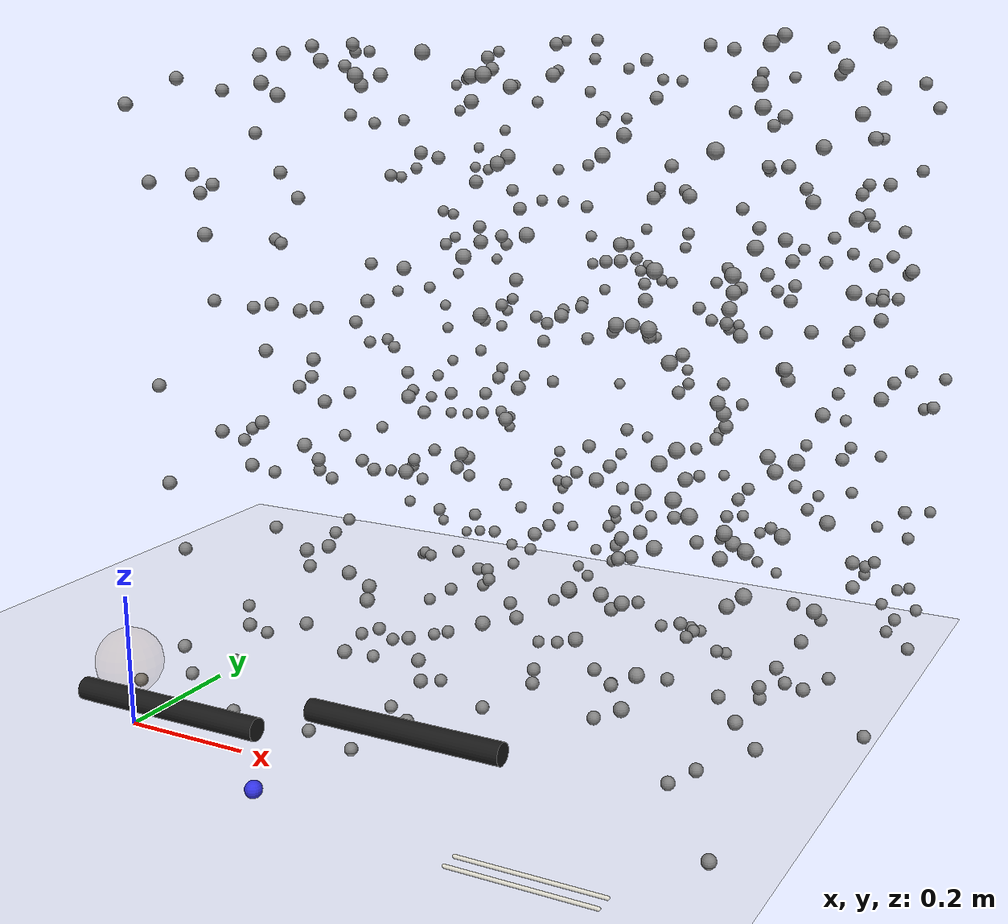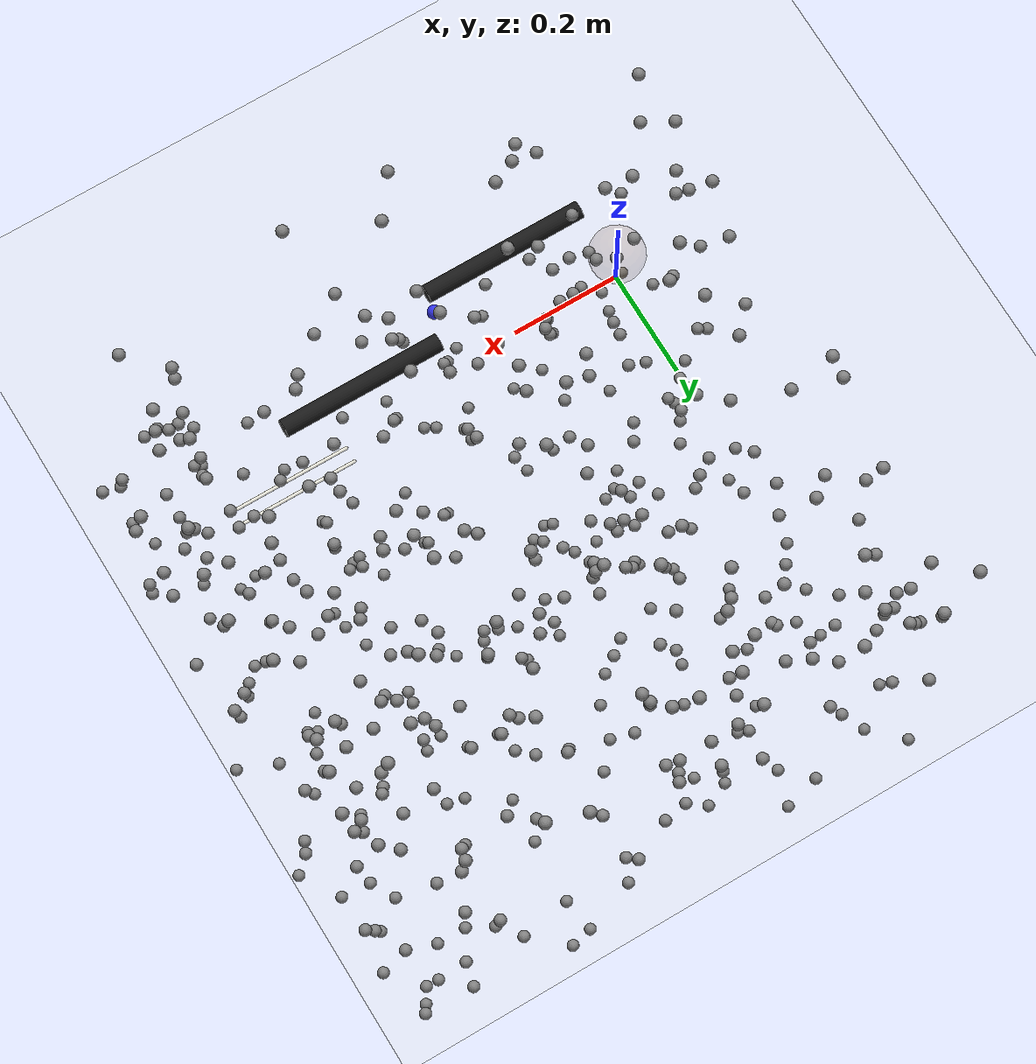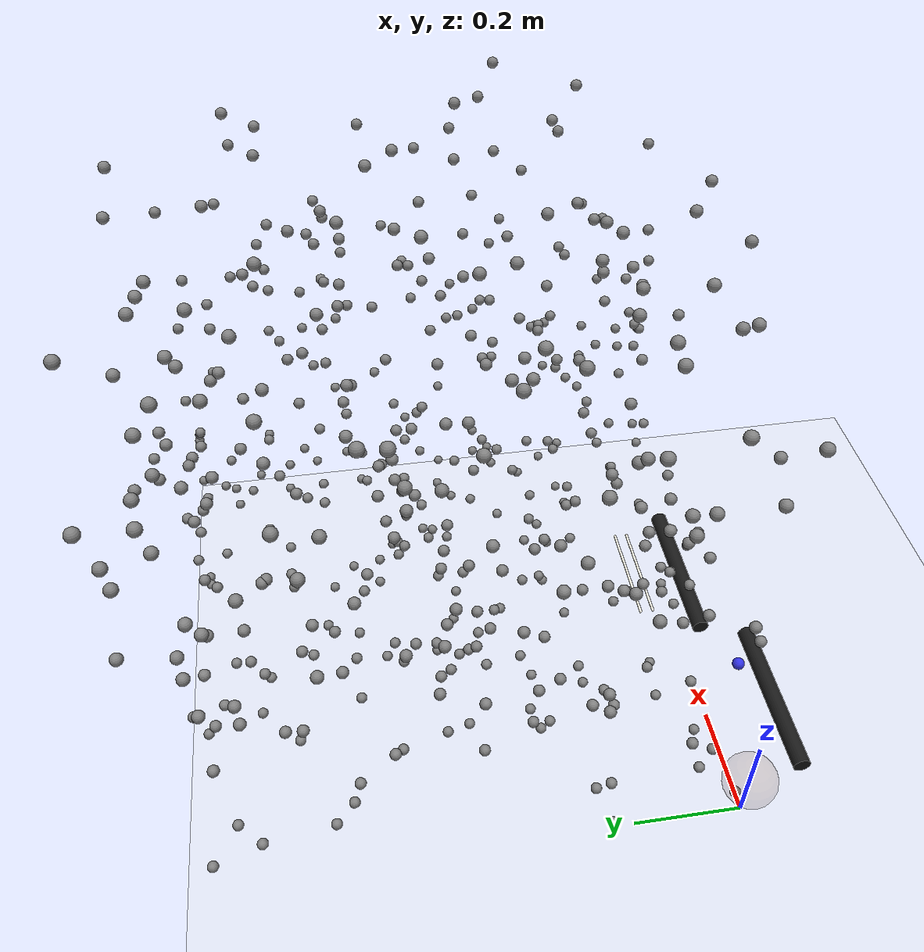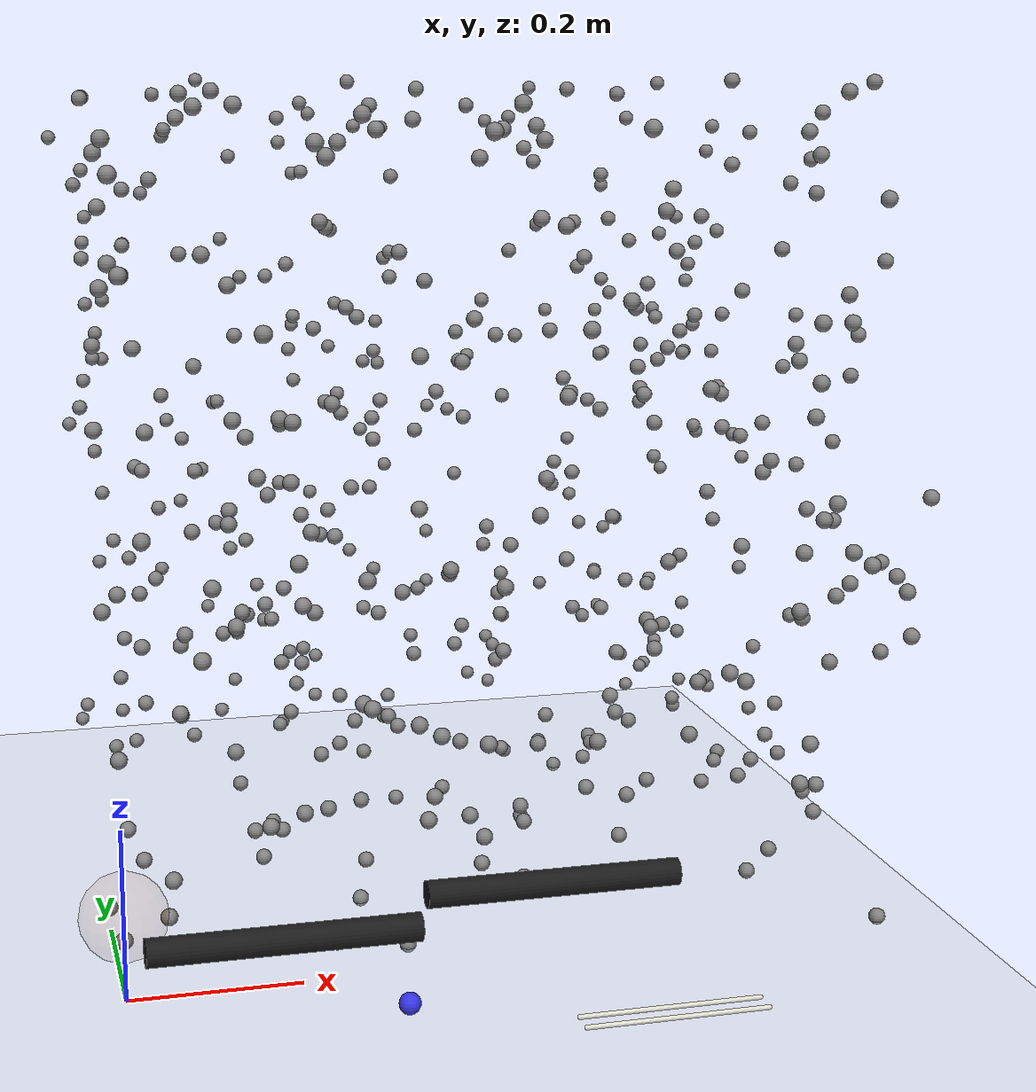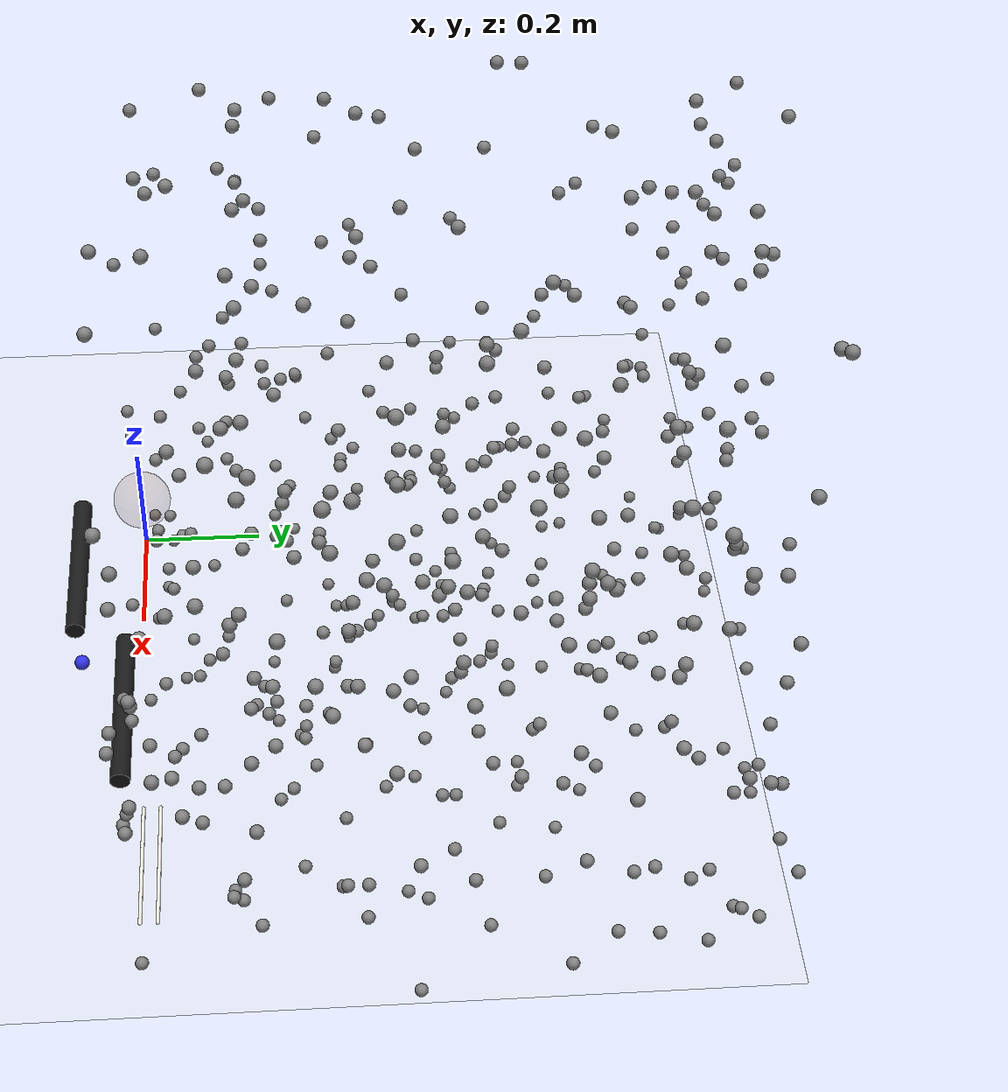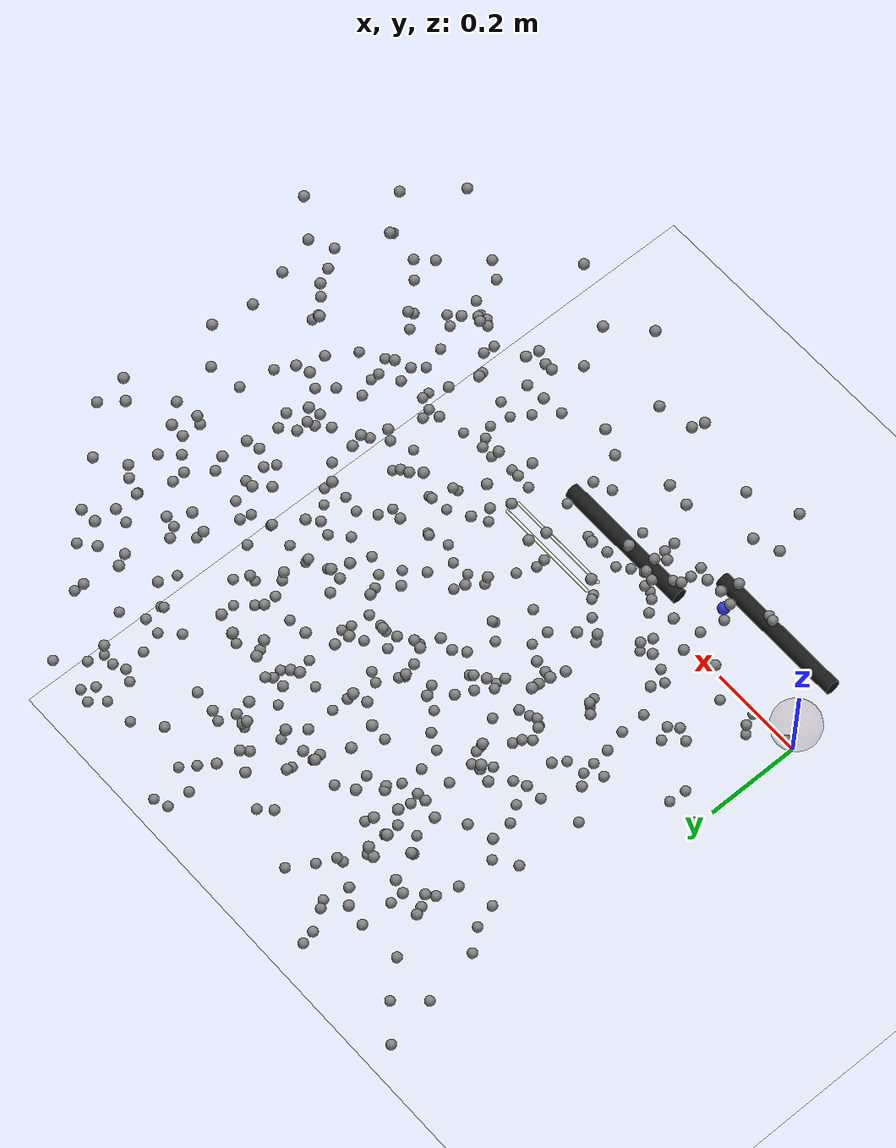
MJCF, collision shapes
<?xml version="1.0" encoding="UTF-8"?>
<mujoco model="hebi">
    <compiler angle="radian" meshdir="meshes/"/>

    <size njmax="500" nconmax="100"/>

    <option timestep="0.0005" cone="elliptic" impratio="3">
    </option>

    <asset>
        <mesh name="X8" file="X8.stl" scale="0.001 0.001 0.001"/>
        <mesh name="PM-2149-01" file="PM-2149-01.stl" scale="0.001 0.001 0.001"/>
        <mesh name="PM-2150-01R" file="PM-2150-01R.stl" scale="0.001 0.001 0.001"/>
        <mesh name="A-2038-02" file="A-2038-02.stl"/>
        <mesh name="A-2039-02" file="A-2039-02.stl"/>
        <mesh name="X5" file="X5.stl" scale="0.001 0.001 0.001"/>
        <mesh name="PM-2132-01R" file="PM-2132-01R.stl" scale="0.001 0.001 0.001"/>
        <mesh name="PM-2132-01L" file="PM-2132-01L.stl" scale="0.001 0.001 0.001"/>
        <mesh name="chopstick" file="chopstick.stl"/>
        <mesh name="chopstick_collision" file="chopstick_collision.stl"/>
        <mesh name="chopstick_mount_m3" file="chopstick_mount_m3.stl"/>
        <mesh name="chopstick_mount_m5" file="chopstick_mount_m5.stl"/>

        <material name="floor_mat" specular="0.5" shininess="0.5" reflectance="0.5" rgba="0.2 0.2 0.2 1"/>
        <material name="table_mat" specular="0.5" shininess="0.5" reflectance="0.5" rgba="0.93 0.93 0.93 1"/>
        <material name="block_mat" specular="0" shininess="0.5" reflectance="0" rgba="0.2 0.2 0.2 1"/>
        <material name="motor" specular="0" shininess="0.5" reflectance="0" rgba="0.82 0.06 0.06 1"/>
        <material name="contact" specular="0" shininess="0.5" reflectance="0" rgba="0.06 0.06 0.82 0.5"/>
    </asset>

    <default>
        <geom contype="0" conaffinity="0" group="0"/>
        <site rgba="1 1 0 0.3"/>

        <default class="con">
            <geom contype="1" conaffinity="1" condim="6" group="1" friction="0.4 0.002 0.00008" solref="0.0035 1"/>
        </default>

        <default class="X8">
            <joint damping="16.92" armature="1.204" frictionloss="1.295" limited="false"/>
            <position forcelimited="true" forcerange="-20 20"/>
            <velocity ctrllimited="true" ctrlrange="-0.001 0.001"/>
            <motor forcelimited="true" forcerange="-20 20" ctrllimited="true" ctrlrange="-1 1"/>
            <general ctrllimited="false"/>
        </default>

        <default class="X8_16">
            <joint damping="43.95" armature="2.12" frictionloss="2.343" limited="false"/>
            <position forcelimited="true" forcerange="-20 20"/>
            <velocity ctrllimited="true" ctrlrange="-0.001 0.001"/>
            <motor forcelimited="true" forcerange="-38 38" ctrllimited="true" ctrlrange="-1 1"/>
            <general ctrllimited="false"/>
        </default>

        <default class="X5">
            <joint damping="3.77" armature="1.29" frictionloss="1.00" limited="false"/>
            <position forcelimited="true" forcerange="-2.5 2.5"/>
            <velocity ctrllimited="true" ctrlrange="-0.001 0.001"/>
            <motor forcelimited="true" forcerange="-2.5 2.5" ctrllimited="true" ctrlrange="-1 1"/>
            <general ctrllimited="false"/>
        </default>
    </default>

    <worldbody>
        <light diffuse=".5 .5 .5" pos="0 0 3" dir="0 0 -1" castshadow="true"/>

        <!-- Arena -->
        <geom name="ground" class="con" pos="0 0 0" rgba="0.9 0.9 0.9 1" size="1 1 10" type="plane" material="table_mat"/>

        <camera name="realsense" mode="fixed" pos="0 0 0.3" xyaxes="0 -1 0 0 0 -1"/>

        <geom name="centroid" pos="0 0 0.1" type="sphere" size="0.05" rgba="0.5 0.3 0.05 0.1"/>

        <!-- Arm -->
        <geom type="mesh" material="motor" mesh="X8"/>
        <body name="shoulder_bracket" pos="0 0 0.045">
            <inertial pos="-0.0101399 -0.048785 0.0445629" quat="0.720398 0.150702 -0.477883 0.479525" mass="0.715" diaginertia="0.00110899 0.00102189 0.000683866"/>
            <joint class="X8" name="HEBI/base/X8_9" pos="0 0 0" axis="0 0 1" range="-6.28319 3.14159"/>
            <geom pos="0 0 0.005" quat="0.5 0.5 0.5 0.5" type="mesh" rgba="0.1 0.1 0.1 1" mesh="PM-2149-01"/>
            <geom pos="0 -0.03 0.04" quat="0.707107 0.707107 0 0" type="mesh" rgba="0.1 0.1 0.1 1" mesh="PM-2150-01R"/>
            <geom pos="0 -0.0375 0.055" quat="0.707107 0.707107 0 0" type="mesh" material="motor" mesh="X8"/>
            <body name="shoulder_elbow" pos="0 -0.0825 0.055" quat="0.707107 0.707107 0 0">
                <inertial pos="0.243044 0.00168707 -0.00405442" quat="0.431216 0.559464 0.519497 0.480808" mass="0.882" diaginertia="0.0091413 0.00903082 0.000436897"/>
                <joint class="X8_16" name="HEBI/shoulder/X8_16" pos="0 0 0" axis="0 0 1" range="-0.5 3.14159"/>
                <geom type="mesh" rgba="0.1 0.1 0.1 1" mesh="A-2038-02"/>
                <geom size="0.016 0.1498" pos="0.1625 0 0.02" quat="0.707123 0 0.70709 0" type="cylinder" rgba="0.1 0.1 0.1 1"/>
                <geom pos="0.325 0 0" quat="0 -1 0 0" type="mesh" rgba="0.1 0.1 0.1 1" mesh="A-2039-02"/>
                <geom pos="0.325 0 0" quat="0 1 0 0" type="mesh" material="motor" mesh="X8"/>
                <body name="elbow_wrist1" pos="0.325 0 -0.045" quat="0 1 0 0">
                    <inertial pos="0.227653 0.00136192 0.00396444" quat="0.38535 0.602736 0.44622 0.537683" mass="0.717" diaginertia="0.00791717 0.00789062 0.000266423"/>
                    <joint class="X8" name="HEBI/elbow/X8_9" pos="0 0 0" axis="0 0 1" range="-3 3"/>
                    <geom type="mesh" rgba="0.1 0.1 0.1 1" mesh="A-2038-02"/>
                    <geom size="0.016 0.1498" pos="0.1625 0 0.02" quat="0.707123 0 0.70709 0" type="cylinder" rgba="0.1 0.1 0.1 1"/>
                    <geom pos="0.325 0 0" quat="0 -1 0 0" type="mesh" rgba="0.1 0.1 0.1 1" mesh="A-2039-02"/>
                    <geom pos="0.325 0 0" quat="0 1 0 0" type="mesh" material="motor" mesh="X5"/>
                    <body name="wrist1_wrist2" pos="0.325 0 -0.031" quat="0 1 0 0">
                        <inertial pos="-0.0107783 -0.0503434 0.0328277" quat="0.085146 0.689429 0.478781 0.536849" mass="0.415" diaginertia="0.000574146 0.000532257 0.000373775"/>
                        <joint class="X5" name="HEBI/wrist1/X5_1" pos="0 0 0" axis="0 0 1" limited="false" range="-6.28319 6.28319"/>
                        <geom quat="0.5 0.5 -0.5 -0.5" type="mesh" rgba="0.96 0.945 0.871 1" mesh="PM-2132-01R"/>
                        <geom pos="0 -0.043 0.04" quat="0.707107 0.707107 0 0" type="mesh" material="motor" mesh="X5"/>
                        <body name="wrist2_wrist3" pos="0 -0.074 0.04" quat="0.707107 0.707107 0 0">
                            <inertial pos="-0.0107783 -0.0503434 0.0328277" quat="0.085146 0.689429 0.478781 0.536849" mass="0.415" diaginertia="0.000574146 0.000532257 0.000373775"/>
                            <joint class="X5" name="HEBI/wrist2/X5_1" pos="0 0 0" axis="0 0 1" limited="false" range="-4.71239 4.71239"/>
                            <geom quat="0.5 0.5 -0.5 -0.5" type="mesh" rgba="0.96 0.945 0.871 1" mesh="PM-2132-01R"/>
                            <geom pos="0 -0.043 0.04" quat="0.707107 0.707107 0 0" type="mesh" material="motor" mesh="X5"/>
                            <body name="wrist3_chopstick" pos="0 -0.074 0.04" quat="0.707107 0.707107 0 0">
                                <joint class="X5" name="HEBI/wrist3/X5_1" pos="0 0 0" axis="0 0 1"/>
                                <geom quat="0.5 0.5 0.5 0.5" type="mesh" rgba="0.96 0.945 0.871 1" mesh="PM-2132-01L"/>
                                <geom pos="0 0.043 0.04" quat="0.707107 -0.707107 0 0" type="mesh" material="motor" mesh="X5"/>

                                <geom name="stick" class="con" pos="0.001 0.079024 0.06325" type="capsule" quat="0.707 0 0.707 0" rgba="0.96 0.945 0.871 0.3" size="0.003 0.115"/>
                                <site name="stick" pos="0.116 0.079024 0.06325" quat="0.707 0 0.707 0" type="sphere" size="0.004"/>

                                <body name="end_effector" pos="0 0.074 0.04" quat="0.707107 -0.707107 0 0">

                                    <joint class="X5" name="HEBI/chopstick/X5_1" pos="0 0 0" axis="0 0 1"/>
                                    <geom name="chop" class="con" pos="0.001 0.0048 0.005274" quat="0.5 0.5 0.5 0.5" type="capsule" rgba="0.96 0.945 0.871 0.3" size="0.003 0.115"/>
                                    <site name="chop" pos="0.116 0.0048 0.005274" quat="0.5 0.5 0.5 0.5" type="sphere" size="0.004"/>
                                </body>
                            </body>
                        </body>
                    </body>
                </body>
            </body>
        </body>

        <!-- For interactively tracking a end effector pose -->
        <body name="pose" pos="0.7 0 0.1" xyaxes="0 -1 0 0 0 -1" mocap="true">
            <geom name="pose" rgba="0 1 0 0" type="capsule" size="0.005 0.01"/>
            <site name="pose" rgba="0.9 0.2 0.2 0" type="sphere" size="0.005"/>
        </body>

        <!-- Object to pickup -->
        <body name="obj" pos="0.3 -0.1 0.01">
            <geom name="obj" priority="10" class="con" rgba="0.2 0.2 0.9 0" type="sphere" size="0.0125"/>
            <joint type="free"/>
        </body>
        <!-- Object's goal pose -->
        <body name="goal" pos="0.6 0.03 0.1" mocap="true">
            <geom name="goal" rgba="0.2 0.2 0.9 0" type="sphere" size="0.0125"/>
            <site name="goal" rgba="0.2 0.2 0.9 0" type="sphere" size="0.0125"/>
        </body>
    <geom type="sphere" name="point_1" size="0.01" contype="0" conaffinity="0" pos="0.8887773154426111 0.12472228269227403 0.3785849554604255"/><geom type="sphere" name="point_2" size="0.01" contype="0" conaffinity="0" pos="0.36327360588907087 0.6026863440151748 0.550574459034538"/><geom type="sphere" name="point_3" size="0.01" contype="0" conaffinity="0" pos="0.013793435428259393 0.8959690052223312 0.5006175517853737"/><geom type="sphere" name="point_4" size="0.01" contype="0" conaffinity="0" pos="0.8046471507889481 0.4709886947904387 0.6666023843889741"/><geom type="sphere" name="point_5" size="0.01" contype="0" conaffinity="0" pos="0.6260362147469503 0.7033480138852477 0.01253142049998135"/><geom type="sphere" name="point_6" size="0.01" contype="0" conaffinity="0" pos="0.6030025898208156 0.40786797174860423 0.681233048506326"/><geom type="sphere" name="point_7" size="0.01" contype="0" conaffinity="0" pos="0.6880601706191802 0.30364793862563677 0.6448668659358001"/><geom type="sphere" name="point_8" size="0.01" contype="0" conaffinity="0" pos="0.034156919376081785 0.1983239516121711 0.785212982670618"/><geom type="sphere" name="point_9" size="0.01" contype="0" conaffinity="0" pos="0.17761377797931877 0.5138056807001206 0.4251559655289485"/><geom type="sphere" name="point_10" size="0.01" contype="0" conaffinity="0" pos="0.1108335213625018 0.3689535860337836 0.3008453516081879"/><geom type="sphere" name="point_11" size="0.01" contype="0" conaffinity="0" pos="0.5337784949703055 0.20309951430323925 0.9323159620863952"/><geom type="sphere" name="point_12" size="0.01" contype="0" conaffinity="0" pos="0.8905833530334337 0.02641145675661627 0.8690283365413742"/><geom type="sphere" name="point_13" size="0.01" contype="0" conaffinity="0" pos="0.22233149494104665 0.17543567763817536 0.5426527889022861"/><geom type="sphere" name="point_14" size="0.01" contype="0" conaffinity="0" pos="0.5664231496427587 0.7745329603047373 0.4243771620015222"/><geom type="sphere" name="point_15" size="0.01" contype="0" conaffinity="0" pos="0.1474640574372854 0.11932528757895278 0.3889010024638224"/><geom type="sphere" name="point_16" size="0.01" contype="0" conaffinity="0" pos="0.3547159576023058 0.48836491167691043 0.46906715344451455"/><geom type="sphere" name="point_17" size="0.01" contype="0" conaffinity="0" pos="0.9199763391096931 0.7671673607868803 0.5969402799124544"/><geom type="sphere" name="point_18" size="0.01" contype="0" conaffinity="0" pos="0.27546737113825315 0.24877647164374173 0.11297463215648107"/><geom type="sphere" name="point_19" size="0.01" contype="0" conaffinity="0" pos="0.978971636039961 0.182123918837805 0.2854676561348777"/><geom type="sphere" name="point_20" size="0.01" contype="0" conaffinity="0" pos="0.6716855892322282 0.5690287658189903 0.9863858472970652"/><geom type="sphere" name="point_21" size="0.01" contype="0" conaffinity="0" pos="0.2565038733270619 0.5609548293252826 0.2759326494543781"/><geom type="sphere" name="point_22" size="0.01" contype="0" conaffinity="0" pos="0.4631333853210624 0.32463601706362666 0.16126707927274841"/><geom type="sphere" name="point_23" size="0.01" contype="0" conaffinity="0" pos="0.7961297134672889 0.9392345851436863 0.3493261647360604"/><geom type="sphere" name="point_24" size="0.01" contype="0" conaffinity="0" pos="0.6489279095636542 0.6003682057948461 0.059026624826435725"/><geom type="sphere" name="point_25" size="0.01" contype="0" conaffinity="0" pos="0.1125674912471597 0.3334028083725713 0.3242169475139316"/><geom type="sphere" name="point_26" size="0.01" contype="0" conaffinity="0" pos="0.012607474621597836 0.2568470141216048 0.9203349647743269"/><geom type="sphere" name="point_27" size="0.01" contype="0" conaffinity="0" pos="0.6104737459768905 0.10257210963879326 0.7515912357491747"/><geom type="sphere" name="point_28" size="0.01" contype="0" conaffinity="0" pos="0.3776682374131701 0.17926755761429725 0.6850245870631257"/><geom type="sphere" name="point_29" size="0.01" contype="0" conaffinity="0" pos="0.6536987217498125 0.9173678140940431 0.1302963269760602"/><geom type="sphere" name="point_30" size="0.01" contype="0" conaffinity="0" pos="0.02141337084911732 0.747985497064388 0.8571181824833163"/><geom type="sphere" name="point_31" size="0.01" contype="0" conaffinity="0" pos="0.09666640887796296 0.4712053772652245 0.8776811273407465"/><geom type="sphere" name="point_32" size="0.01" contype="0" conaffinity="0" pos="0.8951868370353366 0.7050791300943025 0.6032829892226608"/><geom type="sphere" name="point_33" size="0.01" contype="0" conaffinity="0" pos="0.8569111613416924 0.4838674327718959 0.17366969386488806"/><geom type="sphere" name="point_34" size="0.01" contype="0" conaffinity="0" pos="0.7199133943126921 0.3296144437804631 0.08594934727409198"/><geom type="sphere" name="point_35" size="0.01" contype="0" conaffinity="0" pos="0.290794286148061 0.5199802985500022 0.22312466423998"/><geom type="sphere" name="point_36" size="0.01" contype="0" conaffinity="0" pos="0.9355180487008123 0.5659115190919521 0.9269742393969238"/><geom type="sphere" name="point_37" size="0.01" contype="0" conaffinity="0" pos="0.41775220290226445 0.9289904563412021 0.6644255040963738"/><geom type="sphere" name="point_38" size="0.01" contype="0" conaffinity="0" pos="0.400418447545271 0.5907144043226249 0.4472277099602002"/><geom type="sphere" name="point_39" size="0.01" contype="0" conaffinity="0" pos="0.9743237566286682 0.6570444797024508 0.2851264624287666"/><geom type="sphere" name="point_40" size="0.01" contype="0" conaffinity="0" pos="0.1855058978069939 0.525196459923509 0.2697573170101526"/><geom type="sphere" name="point_41" size="0.01" contype="0" conaffinity="0" pos="0.39321457097913126 0.6094662672324183 0.06001010737402468"/><geom type="sphere" name="point_42" size="0.01" contype="0" conaffinity="0" pos="0.3634871487528355 0.48602093987969397 0.6961055942213374"/><geom type="sphere" name="point_43" size="0.01" contype="0" conaffinity="0" pos="0.9973050955961926 0.39197179968926377 0.5201282441473509"/><geom type="sphere" name="point_44" size="0.01" contype="0" conaffinity="0" pos="0.9537244306170309 0.39490430243201846 0.8975360759072009"/><geom type="sphere" name="point_45" size="0.01" contype="0" conaffinity="0" pos="0.19217564240912033 0.330220319729537 0.5709366559083986"/><geom type="sphere" name="point_46" size="0.01" contype="0" conaffinity="0" pos="0.8245408800050547 0.6414816304628337 0.27315499423322165"/><geom type="sphere" name="point_47" size="0.01" contype="0" conaffinity="0" pos="0.9971969316271068 0.5302902352280323 0.6760945985204774"/><geom type="sphere" name="point_48" size="0.01" contype="0" conaffinity="0" pos="0.7762199997217216 0.4392812023957604 0.6488643862312247"/><geom type="sphere" name="point_49" size="0.01" contype="0" conaffinity="0" pos="0.07138322482619852 0.9970766249798584 0.5813163020999874"/><geom type="sphere" name="point_50" size="0.01" contype="0" conaffinity="0" pos="0.2031408099452845 0.5135032710133398 0.06099493986339888"/><geom type="sphere" name="point_51" size="0.01" contype="0" conaffinity="0" pos="0.8140931069883524 0.022831293578466028 0.6604728734912984"/><geom type="sphere" name="point_52" size="0.01" contype="0" conaffinity="0" pos="0.6800083963109862 0.6390677721525404 0.4614480342614171"/><geom type="sphere" name="point_53" size="0.01" contype="0" conaffinity="0" pos="0.9975437099811895 0.30644757593871996 0.9972007856257863"/><geom type="sphere" name="point_54" size="0.01" contype="0" conaffinity="0" pos="0.0012200258558172639 0.22970308881594104 0.6043340012811826"/><geom type="sphere" name="point_55" size="0.01" contype="0" conaffinity="0" pos="0.46743413521436006 0.22895375650296268 0.030577810057844435"/><geom type="sphere" name="point_56" size="0.01" contype="0" conaffinity="0" pos="0.4171115887404715 0.5954619521083999 0.567064008524665"/><geom type="sphere" name="point_57" size="0.01" contype="0" conaffinity="0" pos="0.0367991705727857 0.9070513154721402 0.5624390081174881"/><geom type="sphere" name="point_58" size="0.01" contype="0" conaffinity="0" pos="0.26386445035390094 0.26255643843178755 0.36129900913230406"/><geom type="sphere" name="point_59" size="0.01" contype="0" conaffinity="0" pos="0.41295838574184796 0.3703094024941318 0.9526361262424587"/><geom type="sphere" name="point_60" size="0.01" contype="0" conaffinity="0" pos="0.943595208512904 0.9709485478119748 0.19502740802290042"/><geom type="sphere" name="point_61" size="0.01" contype="0" conaffinity="0" pos="0.1475606697345535 0.7565616542977547 0.9304988479140139"/><geom type="sphere" name="point_62" size="0.01" contype="0" conaffinity="0" pos="0.05112207419325321 0.9100684105601369 0.5948319775437765"/><geom type="sphere" name="point_63" size="0.01" contype="0" conaffinity="0" pos="0.8170807494777115 0.03089820562034573 0.7287041128583349"/><geom type="sphere" name="point_64" size="0.01" contype="0" conaffinity="0" pos="0.4411206063580384 0.4965909888100122 0.23255040476348898"/><geom type="sphere" name="point_65" size="0.01" contype="0" conaffinity="0" pos="0.9152687890196163 0.20031697407972127 0.45613495150785477"/><geom type="sphere" name="point_66" size="0.01" contype="0" conaffinity="0" pos="0.09874400729384569 0.5377246953141519 0.3476971045770356"/><geom type="sphere" name="point_67" size="0.01" contype="0" conaffinity="0" pos="0.33181990766450276 0.747469499797774 0.1783087529651992"/><geom type="sphere" name="point_68" size="0.01" contype="0" conaffinity="0" pos="0.10022382774560601 0.9144759468581372 0.7611538964262794"/><geom type="sphere" name="point_69" size="0.01" contype="0" conaffinity="0" pos="0.13167906765964066 0.3958880602471122 0.440589886453143"/><geom type="sphere" name="point_70" size="0.01" contype="0" conaffinity="0" pos="0.8630861946469504 0.31956105751886166 0.1059481010067247"/><geom type="sphere" name="point_71" size="0.01" contype="0" conaffinity="0" pos="0.8612427419051552 0.8650238999772946 0.10098443033511817"/><geom type="sphere" name="point_72" size="0.01" contype="0" conaffinity="0" pos="0.6222866309674437 0.2876497719500448 0.09808824629084834"/><geom type="sphere" name="point_73" size="0.01" contype="0" conaffinity="0" pos="0.08037275217185447 0.6930767166874114 0.777699682032853"/><geom type="sphere" name="point_74" size="0.01" contype="0" conaffinity="0" pos="0.4820965229023928 0.8343350430848668 0.7487362768198127"/><geom type="sphere" name="point_75" size="0.01" contype="0" conaffinity="0" pos="0.13104133578687693 0.23475449502768675 0.8037873086174872"/><geom type="sphere" name="point_76" size="0.01" contype="0" conaffinity="0" pos="0.16009470045976038 0.2554431415778857 0.4958274167253973"/><geom type="sphere" name="point_77" size="0.01" contype="0" conaffinity="0" pos="0.22078147805481585 0.14987344310786876 0.6176032103201969"/><geom type="sphere" name="point_78" size="0.01" contype="0" conaffinity="0" pos="0.28192246816208244 0.22984555389825534 0.6244674079840118"/><geom type="sphere" name="point_79" size="0.01" contype="0" conaffinity="0" pos="0.4609493886944731 0.22629720842986845 0.9112533816993627"/><geom type="sphere" name="point_80" size="0.01" contype="0" conaffinity="0" pos="0.8670545826227216 0.48810189740468 0.58557814395924"/><geom type="sphere" name="point_81" size="0.01" contype="0" conaffinity="0" pos="0.35483003168225213 0.042675402815872676 0.16540246308234252"/><geom type="sphere" name="point_82" size="0.01" contype="0" conaffinity="0" pos="0.6887288442878208 0.2211054941365722 0.29884759369059277"/><geom type="sphere" name="point_83" size="0.01" contype="0" conaffinity="0" pos="0.1757796508202012 0.9124620177691798 0.37404195822701913"/><geom type="sphere" name="point_84" size="0.01" contype="0" conaffinity="0" pos="0.6881110869464164 0.08923039992545001 0.2279341649989426"/><geom type="sphere" name="point_85" size="0.01" contype="0" conaffinity="0" pos="0.14479191886699327 0.9107539542343692 0.2710841536716715"/><geom type="sphere" name="point_86" size="0.01" contype="0" conaffinity="0" pos="0.48523559431971597 0.9504633400465272 0.6326546074376156"/><geom type="sphere" name="point_87" size="0.01" contype="0" conaffinity="0" pos="0.7219395465059462 0.13250581556251717 0.6406351875729484"/><geom type="sphere" name="point_88" size="0.01" contype="0" conaffinity="0" pos="0.8505536947475698 0.6951185130904496 0.4519296145105327"/><geom type="sphere" name="point_89" size="0.01" contype="0" conaffinity="0" pos="0.16837894008664267 0.014210375209504411 0.7375985855561946"/><geom type="sphere" name="point_90" size="0.01" contype="0" conaffinity="0" pos="0.04536856169910197 0.9617927894640468 0.7606247268929625"/><geom type="sphere" name="point_91" size="0.01" contype="0" conaffinity="0" pos="0.036686852097722156 0.05586649468810467 0.5086869483158982"/><geom type="sphere" name="point_92" size="0.01" contype="0" conaffinity="0" pos="0.3102081919482791 0.22344311025927932 0.0017286421299085308"/><geom type="sphere" name="point_93" size="0.01" contype="0" conaffinity="0" pos="0.012947517351114879 0.3724242800570585 0.6840469010812982"/><geom type="sphere" name="point_94" size="0.01" contype="0" conaffinity="0" pos="0.8886944301544855 0.6458232371275276 0.7697935349944784"/><geom type="sphere" name="point_95" size="0.01" contype="0" conaffinity="0" pos="0.45497340703204747 0.8203750945479835 0.6050656725635033"/><geom type="sphere" name="point_96" size="0.01" contype="0" conaffinity="0" pos="0.47846967916564753 0.905627845297208 0.5747369867187333"/><geom type="sphere" name="point_97" size="0.01" contype="0" conaffinity="0" pos="0.6246305669632632 0.20158181339999448 0.24748514141892008"/><geom type="sphere" name="point_98" size="0.01" contype="0" conaffinity="0" pos="0.02130275482166777 0.952432670150166 0.029954655805130903"/><geom type="sphere" name="point_99" size="0.01" contype="0" conaffinity="0" pos="0.5880917784990509 0.9069115907253089 0.4990219222258727"/><geom type="sphere" name="point_100" size="0.01" contype="0" conaffinity="0" pos="0.14466096857666355 0.44757540519030803 0.643900382368624"/><geom type="sphere" name="point_101" size="0.01" contype="0" conaffinity="0" pos="0.34608951990703796 0.4333030375557483 0.16367846685940002"/><geom type="sphere" name="point_102" size="0.01" contype="0" conaffinity="0" pos="0.4001024880770925 0.5706210093814588 0.547667276604918"/><geom type="sphere" name="point_103" size="0.01" contype="0" conaffinity="0" pos="0.37737499951464937 0.1849520081257372 0.5014800039423708"/><geom type="sphere" name="point_104" size="0.01" contype="0" conaffinity="0" pos="0.14545702498457413 0.8762377331240736 0.9767034020101977"/><geom type="sphere" name="point_105" size="0.01" contype="0" conaffinity="0" pos="0.1609825972673724 0.23538905545908806 0.7677683001809374"/><geom type="sphere" name="point_106" size="0.01" contype="0" conaffinity="0" pos="0.12228842914806415 0.20809176583550348 0.9725124235966427"/><geom type="sphere" name="point_107" size="0.01" contype="0" conaffinity="0" pos="0.22297638676872467 0.9943373350352123 0.9961426581391257"/><geom type="sphere" name="point_108" size="0.01" contype="0" conaffinity="0" pos="0.6706806590613572 0.9668214937358057 0.04133228185848692"/><geom type="sphere" name="point_109" size="0.01" contype="0" conaffinity="0" pos="0.1755774492545954 0.12615089644967492 0.5599304874701079"/><geom type="sphere" name="point_110" size="0.01" contype="0" conaffinity="0" pos="0.43666124845345666 0.40991936773747484 0.7490064789023994"/><geom type="sphere" name="point_111" size="0.01" contype="0" conaffinity="0" pos="0.8462563804909882 0.03737898907618242 0.5144429560518295"/><geom type="sphere" name="point_112" size="0.01" contype="0" conaffinity="0" pos="0.6875793722410557 0.2334574941939105 0.32376852013356516"/><geom type="sphere" name="point_113" size="0.01" contype="0" conaffinity="0" pos="0.06130201903128296 0.05147599976733663 0.11611024168798134"/><geom type="sphere" name="point_114" size="0.01" contype="0" conaffinity="0" pos="0.5618305421584429 0.940011194557308 0.30100697291732836"/><geom type="sphere" name="point_115" size="0.01" contype="0" conaffinity="0" pos="0.05525896021337995 0.2916927227101982 0.3234351465893315"/><geom type="sphere" name="point_116" size="0.01" contype="0" conaffinity="0" pos="0.6926840865029269 0.6939040088972901 0.41790967151433467"/><geom type="sphere" name="point_117" size="0.01" contype="0" conaffinity="0" pos="0.9218213155846671 0.6176426629826215 0.6693399601741878"/><geom type="sphere" name="point_118" size="0.01" contype="0" conaffinity="0" pos="0.31045038236412226 0.7866298017945368 0.9447892015251511"/><geom type="sphere" name="point_119" size="0.01" contype="0" conaffinity="0" pos="0.794653102510541 0.00029056091735069067 0.18725236523257727"/><geom type="sphere" name="point_120" size="0.01" contype="0" conaffinity="0" pos="0.8270748837881667 0.0304146744681848 0.49745435448919584"/><geom type="sphere" name="point_121" size="0.01" contype="0" conaffinity="0" pos="0.061795665631384056 0.24748517894311095 0.5960897833644132"/><geom type="sphere" name="point_122" size="0.01" contype="0" conaffinity="0" pos="0.23294711181502925 0.16546860853142165 0.39657368602840126"/><geom type="sphere" name="point_123" size="0.01" contype="0" conaffinity="0" pos="0.7016665759247622 0.6110041589548418 0.25257322676618066"/><geom type="sphere" name="point_124" size="0.01" contype="0" conaffinity="0" pos="0.25504843567465607 0.08767971965678512 0.0071634574809038565"/><geom type="sphere" name="point_125" size="0.01" contype="0" conaffinity="0" pos="0.3428218866420114 0.45299117056942784 0.712687739901489"/><geom type="sphere" name="point_126" size="0.01" contype="0" conaffinity="0" pos="0.1299884582980062 0.9266818983895622 0.8336640312623458"/><geom type="sphere" name="point_127" size="0.01" contype="0" conaffinity="0" pos="0.832503974139825 0.20864782673033466 0.535052385786656"/><geom type="sphere" name="point_128" size="0.01" contype="0" conaffinity="0" pos="0.6100413077887825 0.6350321152215215 0.7648830365448784"/><geom type="sphere" name="point_129" size="0.01" contype="0" conaffinity="0" pos="0.01838719838152314 0.17243983449063527 0.8014109518411534"/><geom type="sphere" name="point_130" size="0.01" contype="0" conaffinity="0" pos="0.6922937680531791 0.49984692758486626 0.09597088656963115"/><geom type="sphere" name="point_131" size="0.01" contype="0" conaffinity="0" pos="0.8293591728503305 0.1700895466021044 0.038467993936236455"/><geom type="sphere" name="point_132" size="0.01" contype="0" conaffinity="0" pos="0.890625125826151 0.6786915542962393 0.7361234061616726"/><geom type="sphere" name="point_133" size="0.01" contype="0" conaffinity="0" pos="0.8851902880890101 0.3261561447243799 0.13696318990080236"/><geom type="sphere" name="point_134" size="0.01" contype="0" conaffinity="0" pos="0.9023598768919128 0.3599310300153509 0.783757615743027"/><geom type="sphere" name="point_135" size="0.01" contype="0" conaffinity="0" pos="0.5638167755713943 0.06309968209853123 0.23714636105631293"/><geom type="sphere" name="point_136" size="0.01" contype="0" conaffinity="0" pos="0.3837888408605663 0.45661380175268684 0.3037488102904802"/><geom type="sphere" name="point_137" size="0.01" contype="0" conaffinity="0" pos="0.31511086602311833 0.5055533023187393 0.40340777733922506"/><geom type="sphere" name="point_138" size="0.01" contype="0" conaffinity="0" pos="0.21354574496928258 0.19931983272024567 0.6142883143821314"/><geom type="sphere" name="point_139" size="0.01" contype="0" conaffinity="0" pos="0.6945669350483719 0.7904633742602354 0.7881093327739621"/><geom type="sphere" name="point_140" size="0.01" contype="0" conaffinity="0" pos="0.6969842544397591 0.2760837114302612 0.32168226873474026"/><geom type="sphere" name="point_141" size="0.01" contype="0" conaffinity="0" pos="0.007670151522120916 0.2789470325757697 0.37375311023101254"/><geom type="sphere" name="point_142" size="0.01" contype="0" conaffinity="0" pos="0.8049668809909851 0.033844208106992735 0.458232338612369"/><geom type="sphere" name="point_143" size="0.01" contype="0" conaffinity="0" pos="0.8573575320091082 0.9519122840814525 0.28935256492373695"/><geom type="sphere" name="point_144" size="0.01" contype="0" conaffinity="0" pos="0.6629961315492705 0.3772083793392802 0.5802648665127021"/><geom type="sphere" name="point_145" size="0.01" contype="0" conaffinity="0" pos="0.2259785556808842 0.13108106592230984 0.1531876318630594"/><geom type="sphere" name="point_146" size="0.01" contype="0" conaffinity="0" pos="0.3833874030262081 0.3960843809934722 0.17928044424901524"/><geom type="sphere" name="point_147" size="0.01" contype="0" conaffinity="0" pos="0.3368688703163438 0.874219792096129 0.6038103804559554"/><geom type="sphere" name="point_148" size="0.01" contype="0" conaffinity="0" pos="0.6251597070918922 0.7227956339202102 0.546668745146401"/><geom type="sphere" name="point_149" size="0.01" contype="0" conaffinity="0" pos="0.6489253828567183 0.23011038642973158 0.051427922494185374"/><geom type="sphere" name="point_150" size="0.01" contype="0" conaffinity="0" pos="0.7513656177460668 0.5240440985482502 0.31100200790644217"/><geom type="sphere" name="point_151" size="0.01" contype="0" conaffinity="0" pos="0.5888317861788679 0.7036964184399424 0.6891849370280332"/><geom type="sphere" name="point_152" size="0.01" contype="0" conaffinity="0" pos="0.5528505771187839 0.4104226228559049 0.39756417641305486"/><geom type="sphere" name="point_153" size="0.01" contype="0" conaffinity="0" pos="0.9103870808436441 0.3558911148661408 0.16970069429548307"/><geom type="sphere" name="point_154" size="0.01" contype="0" conaffinity="0" pos="0.9434669031408291 0.7802440125015582 0.48030808924328916"/><geom type="sphere" name="point_155" size="0.01" contype="0" conaffinity="0" pos="0.5001153056197136 0.777151550978298 0.17923166564067539"/><geom type="sphere" name="point_156" size="0.01" contype="0" conaffinity="0" pos="0.6532739500188363 0.47306967847067116 0.81521016317515"/><geom type="sphere" name="point_157" size="0.01" contype="0" conaffinity="0" pos="0.2972415787760505 0.6446851123331843 0.7521277528386712"/><geom type="sphere" name="point_158" size="0.01" contype="0" conaffinity="0" pos="0.3222146153972065 0.5770198501844588 0.6711328044906435"/><geom type="sphere" name="point_159" size="0.01" contype="0" conaffinity="0" pos="0.3417548817402427 0.8571831057638788 0.6551756516908778"/><geom type="sphere" name="point_160" size="0.01" contype="0" conaffinity="0" pos="0.4042231606638882 0.7450008926581535 0.9951618539056597"/><geom type="sphere" name="point_161" size="0.01" contype="0" conaffinity="0" pos="0.8863933180343024 0.15938102078510874 0.12377500542721931"/><geom type="sphere" name="point_162" size="0.01" contype="0" conaffinity="0" pos="0.9441461653254384 0.8158267143812752 0.19234098962670743"/><geom type="sphere" name="point_163" size="0.01" contype="0" conaffinity="0" pos="0.07016361090250944 0.4671187772862402 0.34602881692141385"/><geom type="sphere" name="point_164" size="0.01" contype="0" conaffinity="0" pos="0.8581821610787554 0.38379465185783257 0.7284205191995194"/><geom type="sphere" name="point_165" size="0.01" contype="0" conaffinity="0" pos="0.20615456690141598 0.3324062877528666 0.02407324663236743"/><geom type="sphere" name="point_166" size="0.01" contype="0" conaffinity="0" pos="0.24688297440403728 0.8328102193980107 0.8898339308370111"/><geom type="sphere" name="point_167" size="0.01" contype="0" conaffinity="0" pos="0.9026359513279643 0.170981644206587 0.9872735867962985"/><geom type="sphere" name="point_168" size="0.01" contype="0" conaffinity="0" pos="0.9851381157881423 0.20384116033490152 0.3973281414325751"/><geom type="sphere" name="point_169" size="0.01" contype="0" conaffinity="0" pos="0.08342418417554809 0.5296847997037626 0.4962672603725855"/><geom type="sphere" name="point_170" size="0.01" contype="0" conaffinity="0" pos="0.750100787819834 0.9463531010483848 0.204624370797015"/><geom type="sphere" name="point_171" size="0.01" contype="0" conaffinity="0" pos="0.575719732979199 0.9910730083921486 0.4919952662135374"/><geom type="sphere" name="point_172" size="0.01" contype="0" conaffinity="0" pos="0.2938115582737719 0.3647666841633834 0.8296814465983611"/><geom type="sphere" name="point_173" size="0.01" contype="0" conaffinity="0" pos="0.2395829058707568 0.46676039377734835 0.020291634866942854"/><geom type="sphere" name="point_174" size="0.01" contype="0" conaffinity="0" pos="0.06079051420858406 0.8148417052361119 0.6909188821230945"/><geom type="sphere" name="point_175" size="0.01" contype="0" conaffinity="0" pos="0.4381335685548129 0.10608848400050364 0.11390428829697963"/><geom type="sphere" name="point_176" size="0.01" contype="0" conaffinity="0" pos="0.480865069417852 0.5314197053671117 0.5867235904635453"/><geom type="sphere" name="point_177" size="0.01" contype="0" conaffinity="0" pos="0.9554261514587195 0.8520816223474981 0.056440731188283744"/><geom type="sphere" name="point_178" size="0.01" contype="0" conaffinity="0" pos="0.0573877132286571 0.3280235867865464 0.6848394952347387"/><geom type="sphere" name="point_179" size="0.01" contype="0" conaffinity="0" pos="0.7381135716341254 0.6682032614484557 0.544602098701497"/><geom type="sphere" name="point_180" size="0.01" contype="0" conaffinity="0" pos="0.5316329985659733 0.6267248407076984 0.6545229439293065"/><geom type="sphere" name="point_181" size="0.01" contype="0" conaffinity="0" pos="0.683089060271413 0.16026345638411743 0.42549510664880286"/><geom type="sphere" name="point_182" size="0.01" contype="0" conaffinity="0" pos="0.2829912139737569 0.6679019733688956 0.0904427759500146"/><geom type="sphere" name="point_183" size="0.01" contype="0" conaffinity="0" pos="0.16064498241615333 0.9090950478427295 0.916659726031144"/><geom type="sphere" name="point_184" size="0.01" contype="0" conaffinity="0" pos="0.020288948274352903 0.32229306408494773 0.8542505056196641"/><geom type="sphere" name="point_185" size="0.01" contype="0" conaffinity="0" pos="0.38886624852889806 0.15431846399946791 0.15202133527394257"/><geom type="sphere" name="point_186" size="0.01" contype="0" conaffinity="0" pos="0.6784508353009726 0.1809907530760031 0.8486181261321859"/><geom type="sphere" name="point_187" size="0.01" contype="0" conaffinity="0" pos="0.2178749405168483 0.7905822713067923 0.5429349990871228"/><geom type="sphere" name="point_188" size="0.01" contype="0" conaffinity="0" pos="0.8734808695290028 0.21838318573878746 0.9387331464460789"/><geom type="sphere" name="point_189" size="0.01" contype="0" conaffinity="0" pos="0.39328004123759897 0.3829893087634211 0.16923224005714133"/><geom type="sphere" name="point_190" size="0.01" contype="0" conaffinity="0" pos="0.8175250666421607 0.7503258443666951 0.9426680539866874"/><geom type="sphere" name="point_191" size="0.01" contype="0" conaffinity="0" pos="0.529967353508122 0.2736011724204328 0.0857539521474433"/><geom type="sphere" name="point_192" size="0.01" contype="0" conaffinity="0" pos="0.8254571259806807 0.06041933748502637 0.6143980203284534"/><geom type="sphere" name="point_193" size="0.01" contype="0" conaffinity="0" pos="0.001410900844534213 0.020187048274674213 0.06287345311368786"/><geom type="sphere" name="point_194" size="0.01" contype="0" conaffinity="0" pos="0.0022532522752038986 0.23994869979078404 0.012449225168400524"/><geom type="sphere" name="point_195" size="0.01" contype="0" conaffinity="0" pos="0.011593994227125481 0.048157599400279416 0.9062502064121443"/><geom type="sphere" name="point_196" size="0.01" contype="0" conaffinity="0" pos="0.3921323718830556 0.3570728241347294 0.7908935878930217"/><geom type="sphere" name="point_197" size="0.01" contype="0" conaffinity="0" pos="0.8839144028920378 0.9035872304484529 0.038409692532823"/><geom type="sphere" name="point_198" size="0.01" contype="0" conaffinity="0" pos="0.15952277915979085 0.23505264640212276 0.2000540502583088"/><geom type="sphere" name="point_199" size="0.01" contype="0" conaffinity="0" pos="0.7270003754302878 0.34658868000368503 0.5645758921618671"/><geom type="sphere" name="point_200" size="0.01" contype="0" conaffinity="0" pos="0.5667437253560939 0.9592759192057561 0.21625812894116914"/><geom type="sphere" name="point_201" size="0.01" contype="0" conaffinity="0" pos="0.1940487999587286 0.31983113865575596 0.06508786641641828"/><geom type="sphere" name="point_202" size="0.01" contype="0" conaffinity="0" pos="0.8500700080890504 0.9444880137469573 0.5745047460192192"/><geom type="sphere" name="point_203" size="0.01" contype="0" conaffinity="0" pos="0.47317067445609173 0.08270654652019971 0.976819725096558"/><geom type="sphere" name="point_204" size="0.01" contype="0" conaffinity="0" pos="0.7564829151225174 0.08317748836749095 0.291199963538483"/><geom type="sphere" name="point_205" size="0.01" contype="0" conaffinity="0" pos="0.33793781288685576 0.3246405787095066 0.010929936278049501"/><geom type="sphere" name="point_206" size="0.01" contype="0" conaffinity="0" pos="0.6622313564166409 0.49425141547657847 0.4747646895690796"/><geom type="sphere" name="point_207" size="0.01" contype="0" conaffinity="0" pos="0.027748664279694912 0.7257411151994411 0.7582309440757056"/><geom type="sphere" name="point_208" size="0.01" contype="0" conaffinity="0" pos="0.831526077855794 0.4180265671366812 0.044098841514961906"/><geom type="sphere" name="point_209" size="0.01" contype="0" conaffinity="0" pos="0.7225069068719059 0.4992044975224854 0.4085953641137072"/><geom type="sphere" name="point_210" size="0.01" contype="0" conaffinity="0" pos="0.665621193229839 0.25119547974840284 0.0968540375290583"/><geom type="sphere" name="point_211" size="0.01" contype="0" conaffinity="0" pos="0.2313274569245578 0.41406707633693496 0.47978726208902267"/><geom type="sphere" name="point_212" size="0.01" contype="0" conaffinity="0" pos="0.9588028859056714 0.4271920654969894 0.2718155590091116"/><geom type="sphere" name="point_213" size="0.01" contype="0" conaffinity="0" pos="0.6959368925977456 0.2080360347793575 0.8728108206238347"/><geom type="sphere" name="point_214" size="0.01" contype="0" conaffinity="0" pos="0.9444342453784265 0.3425275626366331 0.9588845775924248"/><geom type="sphere" name="point_215" size="0.01" contype="0" conaffinity="0" pos="0.30622504603672174 0.39393459200725256 0.8209867196458467"/><geom type="sphere" name="point_216" size="0.01" contype="0" conaffinity="0" pos="0.578553902810166 0.4438896858648478 0.007191204653222094"/><geom type="sphere" name="point_217" size="0.01" contype="0" conaffinity="0" pos="0.8762987304556205 0.34671227511274916 0.5582064676374103"/><geom type="sphere" name="point_218" size="0.01" contype="0" conaffinity="0" pos="0.5154923531041886 0.5660899133019672 0.22257118701589085"/><geom type="sphere" name="point_219" size="0.01" contype="0" conaffinity="0" pos="0.7949009668721614 0.15607989628491392 0.01788660876380499"/><geom type="sphere" name="point_220" size="0.01" contype="0" conaffinity="0" pos="0.8308773856611691 0.4693242952688801 0.8201773305525195"/><geom type="sphere" name="point_221" size="0.01" contype="0" conaffinity="0" pos="0.9834833816328845 0.07185994344287261 0.5081699009398994"/><geom type="sphere" name="point_222" size="0.01" contype="0" conaffinity="0" pos="0.2882754017954079 0.05774026708431834 0.4496993882786895"/><geom type="sphere" name="point_223" size="0.01" contype="0" conaffinity="0" pos="0.9525605420469498 0.717450370236036 0.08537364603083764"/><geom type="sphere" name="point_224" size="0.01" contype="0" conaffinity="0" pos="0.04137282578908286 0.8833968984643379 0.6778895809166143"/><geom type="sphere" name="point_225" size="0.01" contype="0" conaffinity="0" pos="0.7267586572511127 0.520865647744077 0.9805480024075677"/><geom type="sphere" name="point_226" size="0.01" contype="0" conaffinity="0" pos="0.14959636911479213 0.5026137354087479 0.49817824023364254"/><geom type="sphere" name="point_227" size="0.01" contype="0" conaffinity="0" pos="0.3606729602528629 0.9631845254868863 0.858498569637332"/><geom type="sphere" name="point_228" size="0.01" contype="0" conaffinity="0" pos="0.41157363625559307 0.9528492142823406 0.5958106576813123"/><geom type="sphere" name="point_229" size="0.01" contype="0" conaffinity="0" pos="0.44975657305449235 0.06159671085446772 0.4316654404144671"/><geom type="sphere" name="point_230" size="0.01" contype="0" conaffinity="0" pos="0.2988528015568803 0.4248327358025328 0.12371053088711159"/><geom type="sphere" name="point_231" size="0.01" contype="0" conaffinity="0" pos="0.04328340301864686 0.9090685673336358 0.8689109598322247"/><geom type="sphere" name="point_232" size="0.01" contype="0" conaffinity="0" pos="0.30480115422780196 0.34323877695803073 0.437457916098255"/><geom type="sphere" name="point_233" size="0.01" contype="0" conaffinity="0" pos="0.33153681917303257 0.20208707414007465 0.946072800539326"/><geom type="sphere" name="point_234" size="0.01" contype="0" conaffinity="0" pos="0.8362489311731389 0.5371758356960052 0.33901939184676966"/><geom type="sphere" name="point_235" size="0.01" contype="0" conaffinity="0" pos="0.22866810195241105 0.4323879440818623 0.3310498248407603"/><geom type="sphere" name="point_236" size="0.01" contype="0" conaffinity="0" pos="0.44275907300570405 0.7722009937219578 0.2864206932775235"/><geom type="sphere" name="point_237" size="0.01" contype="0" conaffinity="0" pos="0.05013686748458057 0.9673724181993595 0.7974736295549676"/><geom type="sphere" name="point_238" size="0.01" contype="0" conaffinity="0" pos="0.271022946282544 0.4969164372329824 0.1624082266004494"/><geom type="sphere" name="point_239" size="0.01" contype="0" conaffinity="0" pos="0.8343911168202618 0.6555396097918695 0.6633804014200197"/><geom type="sphere" name="point_240" size="0.01" contype="0" conaffinity="0" pos="0.1549376384249459 0.8861483743878305 0.5024151848764462"/><geom type="sphere" name="point_241" size="0.01" contype="0" conaffinity="0" pos="0.3485995467296499 0.9022812506001614 0.5533472073028147"/><geom type="sphere" name="point_242" size="0.01" contype="0" conaffinity="0" pos="0.3645572812214035 0.8381246101795923 0.07814633104025259"/><geom type="sphere" name="point_243" size="0.01" contype="0" conaffinity="0" pos="0.8775042237621218 0.0032731847619758003 0.44630578159058376"/><geom type="sphere" name="point_244" size="0.01" contype="0" conaffinity="0" pos="0.6674515626093152 0.5573134508090558 0.5946320310627227"/><geom type="sphere" name="point_245" size="0.01" contype="0" conaffinity="0" pos="0.9869343288656713 0.4274722320497075 0.012177510640103861"/><geom type="sphere" name="point_246" size="0.01" contype="0" conaffinity="0" pos="0.8459796798347805 0.40153079788583135 0.8915546827895087"/><geom type="sphere" name="point_247" size="0.01" contype="0" conaffinity="0" pos="0.09367107034230604 0.002205931569739583 0.3846809171036545"/><geom type="sphere" name="point_248" size="0.01" contype="0" conaffinity="0" pos="0.7096729692581882 0.12056034796482207 0.28304036103939123"/><geom type="sphere" name="point_249" size="0.01" contype="0" conaffinity="0" pos="0.8533572460336756 0.9654022019323354 0.15692924574694"/><geom type="sphere" name="point_250" size="0.01" contype="0" conaffinity="0" pos="0.9379697732411889 0.03210516979476541 0.4036225110729379"/><geom type="sphere" name="point_251" size="0.01" contype="0" conaffinity="0" pos="0.376559985321139 0.8985225291977341 0.12246998688889454"/><geom type="sphere" name="point_252" size="0.01" contype="0" conaffinity="0" pos="0.11753531844391651 0.09256522819901591 0.44215878998522995"/><geom type="sphere" name="point_253" size="0.01" contype="0" conaffinity="0" pos="0.6546486669381266 0.8210342908851724 0.18908106408558578"/><geom type="sphere" name="point_254" size="0.01" contype="0" conaffinity="0" pos="0.8250021538104215 0.8936268739817355 0.23438637524304706"/><geom type="sphere" name="point_255" size="0.01" contype="0" conaffinity="0" pos="0.89001843751519 0.08910425115311504 0.4030583377220296"/><geom type="sphere" name="point_256" size="0.01" contype="0" conaffinity="0" pos="0.3806873057069824 0.7617571738566324 0.7884592517242943"/><geom type="sphere" name="point_257" size="0.01" contype="0" conaffinity="0" pos="0.7321794719550945 0.8684294099800449 0.652729201637974"/><geom type="sphere" name="point_258" size="0.01" contype="0" conaffinity="0" pos="0.6285804885427098 0.7824191569872005 0.1546754809660884"/><geom type="sphere" name="point_259" size="0.01" contype="0" conaffinity="0" pos="0.8832721568206578 0.20380542559950054 0.9115229269238079"/><geom type="sphere" name="point_260" size="0.01" contype="0" conaffinity="0" pos="0.9304159331614157 0.8424515094445444 0.7919141729833621"/><geom type="sphere" name="point_261" size="0.01" contype="0" conaffinity="0" pos="0.08557381082431004 0.7914073184789794 0.31819410070907117"/><geom type="sphere" name="point_262" size="0.01" contype="0" conaffinity="0" pos="0.8705830028254655 0.7482388362942476 0.7750740291909735"/><geom type="sphere" name="point_263" size="0.01" contype="0" conaffinity="0" pos="0.4646425577788902 0.026098128581145685 0.09132414500016339"/><geom type="sphere" name="point_264" size="0.01" contype="0" conaffinity="0" pos="0.8102847484335263 0.009886433993957056 0.2316980356699052"/><geom type="sphere" name="point_265" size="0.01" contype="0" conaffinity="0" pos="0.43183975622974446 0.2565911374988381 0.4020135588397591"/><geom type="sphere" name="point_266" size="0.01" contype="0" conaffinity="0" pos="0.6553938055888784 0.27252824928962616 0.2021389635789781"/><geom type="sphere" name="point_267" size="0.01" contype="0" conaffinity="0" pos="0.29326741567018866 0.5820525299081796 0.1757517879039474"/><geom type="sphere" name="point_268" size="0.01" contype="0" conaffinity="0" pos="0.2544331070019925 0.4661971763594117 0.241763987258782"/><geom type="sphere" name="point_269" size="0.01" contype="0" conaffinity="0" pos="0.5395519145906487 0.6426393832185033 0.6118827527442936"/><geom type="sphere" name="point_270" size="0.01" contype="0" conaffinity="0" pos="0.8918441423677179 0.832617688433779 0.6545850478699562"/><geom type="sphere" name="point_271" size="0.01" contype="0" conaffinity="0" pos="0.23373402999792958 0.34913778578527843 0.0520710961287536"/><geom type="sphere" name="point_272" size="0.01" contype="0" conaffinity="0" pos="0.42456280506667654 0.12294415007065251 0.13608351829918663"/><geom type="sphere" name="point_273" size="0.01" contype="0" conaffinity="0" pos="0.5839950405625725 0.2543767252181095 0.6230803454436931"/><geom type="sphere" name="point_274" size="0.01" contype="0" conaffinity="0" pos="0.7346977693082171 0.615455435808121 0.3015764631638169"/><geom type="sphere" name="point_275" size="0.01" contype="0" conaffinity="0" pos="0.8652331237475921 0.39471942428759244 0.5334670069924503"/><geom type="sphere" name="point_276" size="0.01" contype="0" conaffinity="0" pos="0.6626217127468428 0.8325127858574848 0.9428515202101355"/><geom type="sphere" name="point_277" size="0.01" contype="0" conaffinity="0" pos="0.5577098526324 0.501597046006649 0.21485471650118693"/><geom type="sphere" name="point_278" size="0.01" contype="0" conaffinity="0" pos="0.8998777405828091 0.14336817431132132 0.7473562621239311"/><geom type="sphere" name="point_279" size="0.01" contype="0" conaffinity="0" pos="0.44932550669582993 0.6689858419249353 0.8676011483903117"/><geom type="sphere" name="point_280" size="0.01" contype="0" conaffinity="0" pos="0.8596356516771246 0.6199577614531175 0.10200112557411245"/><geom type="sphere" name="point_281" size="0.01" contype="0" conaffinity="0" pos="0.8405053515087262 0.935964853425566 0.8358552778084205"/><geom type="sphere" name="point_282" size="0.01" contype="0" conaffinity="0" pos="0.923648983104919 0.932595403084526 0.06392704827963613"/><geom type="sphere" name="point_283" size="0.01" contype="0" conaffinity="0" pos="0.2086622081856888 0.45987339955546225 0.3113536925816456"/><geom type="sphere" name="point_284" size="0.01" contype="0" conaffinity="0" pos="0.018314270700421575 0.7211052225299046 0.5526304299517228"/><geom type="sphere" name="point_285" size="0.01" contype="0" conaffinity="0" pos="0.8801422410504423 0.7964260893870789 0.9917242684491823"/><geom type="sphere" name="point_286" size="0.01" contype="0" conaffinity="0" pos="0.8372545312255524 0.8309068679205356 0.33085720847103106"/><geom type="sphere" name="point_287" size="0.01" contype="0" conaffinity="0" pos="0.7114607041388314 0.021968515931618082 0.3224194788341883"/><geom type="sphere" name="point_288" size="0.01" contype="0" conaffinity="0" pos="0.09417408683820572 0.2391024767285992 0.2523375570095039"/><geom type="sphere" name="point_289" size="0.01" contype="0" conaffinity="0" pos="0.2805639238109803 0.8541205587686658 0.25175599036101315"/><geom type="sphere" name="point_290" size="0.01" contype="0" conaffinity="0" pos="0.15223762078545033 0.04508415345664085 0.03391123432455578"/><geom type="sphere" name="point_291" size="0.01" contype="0" conaffinity="0" pos="0.24952422597488022 0.07772687144993218 0.921130971483016"/><geom type="sphere" name="point_292" size="0.01" contype="0" conaffinity="0" pos="0.9373520742479555 0.9095715478341775 0.3910550937306856"/><geom type="sphere" name="point_293" size="0.01" contype="0" conaffinity="0" pos="0.023463831970657933 0.5977082977110482 0.9760869124081215"/><geom type="sphere" name="point_294" size="0.01" contype="0" conaffinity="0" pos="0.9232414342623372 0.6610656112876001 0.6105238058203364"/><geom type="sphere" name="point_295" size="0.01" contype="0" conaffinity="0" pos="0.5296023022913172 0.19234835498333602 0.48410907258856684"/><geom type="sphere" name="point_296" size="0.01" contype="0" conaffinity="0" pos="0.7063843740194986 0.5675144050537695 0.04032691736003424"/><geom type="sphere" name="point_297" size="0.01" contype="0" conaffinity="0" pos="0.7077088991631975 0.6281906947546787 0.741440362390851"/><geom type="sphere" name="point_298" size="0.01" contype="0" conaffinity="0" pos="0.2151554890114611 0.7872879842429104 0.08059306453317028"/><geom type="sphere" name="point_299" size="0.01" contype="0" conaffinity="0" pos="0.9654511581782785 0.4946045487152535 0.6092687496137237"/><geom type="sphere" name="point_300" size="0.01" contype="0" conaffinity="0" pos="0.3711073692125282 0.4328046633868241 0.9685984884963856"/><geom type="sphere" name="point_301" size="0.01" contype="0" conaffinity="0" pos="0.22841979479397878 0.7572269715250566 0.3325468639524627"/><geom type="sphere" name="point_302" size="0.01" contype="0" conaffinity="0" pos="0.45078183011969575 0.9035967290201021 0.47379820337532075"/><geom type="sphere" name="point_303" size="0.01" contype="0" conaffinity="0" pos="0.21356251555192274 0.7969673783652369 0.5411376808629775"/><geom type="sphere" name="point_304" size="0.01" contype="0" conaffinity="0" pos="0.37399670153037845 0.9156477276664847 0.377812417457408"/><geom type="sphere" name="point_305" size="0.01" contype="0" conaffinity="0" pos="0.4171464403231415 0.5058384418433575 0.025432368516614456"/><geom type="sphere" name="point_306" size="0.01" contype="0" conaffinity="0" pos="0.3498650817536175 0.06621486796735288 0.27239278391894595"/><geom type="sphere" name="point_307" size="0.01" contype="0" conaffinity="0" pos="0.814078845468615 0.8759999267155754 0.6497652886202123"/><geom type="sphere" name="point_308" size="0.01" contype="0" conaffinity="0" pos="0.9519437027256188 0.6400616008961568 0.48983630755625507"/><geom type="sphere" name="point_309" size="0.01" contype="0" conaffinity="0" pos="0.28189735895739876 0.6338048037649515 0.45064804279619475"/><geom type="sphere" name="point_310" size="0.01" contype="0" conaffinity="0" pos="0.5749156852741855 0.5422580053615229 0.26878271381565333"/><geom type="sphere" name="point_311" size="0.01" contype="0" conaffinity="0" pos="0.5321157146271764 0.26493190908919284 0.06759237058302903"/><geom type="sphere" name="point_312" size="0.01" contype="0" conaffinity="0" pos="0.8336635424146241 0.49372991921315146 0.6845433369875362"/><geom type="sphere" name="point_313" size="0.01" contype="0" conaffinity="0" pos="0.2444739992163012 0.16882649452345944 0.48363668854229425"/><geom type="sphere" name="point_314" size="0.01" contype="0" conaffinity="0" pos="0.525784084102809 0.5658146593972009 0.24886125403958648"/><geom type="sphere" name="point_315" size="0.01" contype="0" conaffinity="0" pos="0.6186559581816202 0.7005129051232313 0.2865206682989814"/><geom type="sphere" name="point_316" size="0.01" contype="0" conaffinity="0" pos="0.07923829696359652 0.9056903610132696 0.053386716559046477"/><geom type="sphere" name="point_317" size="0.01" contype="0" conaffinity="0" pos="0.3565321933717618 0.5935411241989641 0.1503750321888464"/><geom type="sphere" name="point_318" size="0.01" contype="0" conaffinity="0" pos="0.8854695539600601 0.7762836664779929 0.14643399125327083"/><geom type="sphere" name="point_319" size="0.01" contype="0" conaffinity="0" pos="0.5470169404435719 0.052773957871232735 0.7263448669760542"/><geom type="sphere" name="point_320" size="0.01" contype="0" conaffinity="0" pos="0.4336508500291023 0.9101241300682268 0.2841492065486402"/><geom type="sphere" name="point_321" size="0.01" contype="0" conaffinity="0" pos="0.1671595392515257 0.20484183964386404 0.974729294747658"/><geom type="sphere" name="point_322" size="0.01" contype="0" conaffinity="0" pos="0.39946875045692387 0.5592318101475648 0.5199335355410224"/><geom type="sphere" name="point_323" size="0.01" contype="0" conaffinity="0" pos="0.35331692785786695 0.8435554918339789 0.9643289808137039"/><geom type="sphere" name="point_324" size="0.01" contype="0" conaffinity="0" pos="0.29865570599448343 0.6682764204781344 0.19665597189041972"/><geom type="sphere" name="point_325" size="0.01" contype="0" conaffinity="0" pos="0.46398405258219233 0.5887955967986849 0.5251467209993876"/><geom type="sphere" name="point_326" size="0.01" contype="0" conaffinity="0" pos="0.7468562555955442 0.6477310922148838 0.8674069002326581"/><geom type="sphere" name="point_327" size="0.01" contype="0" conaffinity="0" pos="0.32720842206260414 0.8798418768738963 0.907563643942062"/><geom type="sphere" name="point_328" size="0.01" contype="0" conaffinity="0" pos="0.07208813289938232 0.5771733554858065 0.8598514699836246"/><geom type="sphere" name="point_329" size="0.01" contype="0" conaffinity="0" pos="0.1104578236884306 0.3745725629803094 0.20687421648896342"/><geom type="sphere" name="point_330" size="0.01" contype="0" conaffinity="0" pos="0.6694386780809534 0.2601407326738505 0.7253128913476925"/><geom type="sphere" name="point_331" size="0.01" contype="0" conaffinity="0" pos="0.25623275081994645 0.4509199978962921 0.34649739890060816"/><geom type="sphere" name="point_332" size="0.01" contype="0" conaffinity="0" pos="0.023634573237863332 0.8600186640459655 0.08035696923275548"/><geom type="sphere" name="point_333" size="0.01" contype="0" conaffinity="0" pos="0.6008878021483259 0.012218859749044686 0.9508168654548605"/><geom type="sphere" name="point_334" size="0.01" contype="0" conaffinity="0" pos="0.1548089327530946 0.17066282385645382 0.6193275622038259"/><geom type="sphere" name="point_335" size="0.01" contype="0" conaffinity="0" pos="0.8596737074266929 0.1586111498845817 0.34400943110360593"/><geom type="sphere" name="point_336" size="0.01" contype="0" conaffinity="0" pos="0.33713148902811074 0.3500798120640507 0.08330637666959761"/><geom type="sphere" name="point_337" size="0.01" contype="0" conaffinity="0" pos="0.15232995769019197 0.601828975055726 0.1056386009662662"/><geom type="sphere" name="point_338" size="0.01" contype="0" conaffinity="0" pos="0.99426686476077 0.24587025373299887 0.7764967239830851"/><geom type="sphere" name="point_339" size="0.01" contype="0" conaffinity="0" pos="0.8143414874333335 0.33782182310214237 0.6005297820804822"/><geom type="sphere" name="point_340" size="0.01" contype="0" conaffinity="0" pos="0.992243149336091 0.6472478870807292 0.06822044741969613"/><geom type="sphere" name="point_341" size="0.01" contype="0" conaffinity="0" pos="0.9016140402293331 0.1984984065139126 0.07215611128798916"/><geom type="sphere" name="point_342" size="0.01" contype="0" conaffinity="0" pos="0.8114737327307893 0.055606302386620676 0.3818597052292161"/><geom type="sphere" name="point_343" size="0.01" contype="0" conaffinity="0" pos="0.7497102131720681 0.6198503196165035 0.8078831173152785"/><geom type="sphere" name="point_344" size="0.01" contype="0" conaffinity="0" pos="0.8937065953985355 0.23364152720095333 0.46507853577409586"/><geom type="sphere" name="point_345" size="0.01" contype="0" conaffinity="0" pos="0.9498128179871388 0.7490914289677237 0.9299538692021698"/><geom type="sphere" name="point_346" size="0.01" contype="0" conaffinity="0" pos="0.429897421664029 0.24078202138171312 0.41106912760723957"/><geom type="sphere" name="point_347" size="0.01" contype="0" conaffinity="0" pos="0.6017976228407365 0.5334489862510892 0.9097986277462091"/><geom type="sphere" name="point_348" size="0.01" contype="0" conaffinity="0" pos="0.5345892576364353 0.21203065324006243 0.1889243971204091"/><geom type="sphere" name="point_349" size="0.01" contype="0" conaffinity="0" pos="0.7487174065166862 0.36099494806682464 0.2900210689956315"/><geom type="sphere" name="point_350" size="0.01" contype="0" conaffinity="0" pos="0.2349426645797288 0.06251555097754768 0.9369506494375901"/><geom type="sphere" name="point_351" size="0.01" contype="0" conaffinity="0" pos="0.5482552876404998 0.47536562670431315 0.6687968651322751"/><geom type="sphere" name="point_352" size="0.01" contype="0" conaffinity="0" pos="0.44838992182420534 0.5062221278931522 0.9880073354825658"/><geom type="sphere" name="point_353" size="0.01" contype="0" conaffinity="0" pos="0.002383528407392088 0.9669101121767287 0.9140477158326488"/><geom type="sphere" name="point_354" size="0.01" contype="0" conaffinity="0" pos="0.4330759886511577 0.6593835909671146 0.09454017600602116"/><geom type="sphere" name="point_355" size="0.01" contype="0" conaffinity="0" pos="0.9343483412479807 0.7698409963960766 0.6365098104084523"/><geom type="sphere" name="point_356" size="0.01" contype="0" conaffinity="0" pos="0.7692195742022467 0.8017480579471483 0.3338370812100222"/><geom type="sphere" name="point_357" size="0.01" contype="0" conaffinity="0" pos="0.28237794715349285 0.4619504236000904 0.4411899142275717"/><geom type="sphere" name="point_358" size="0.01" contype="0" conaffinity="0" pos="0.7454339214208243 0.7023701553252046 0.21359346796418888"/><geom type="sphere" name="point_359" size="0.01" contype="0" conaffinity="0" pos="0.7357907321712465 0.9797374883611345 0.9836264668942805"/><geom type="sphere" name="point_360" size="0.01" contype="0" conaffinity="0" pos="0.1215019475162864 0.3377189192772634 0.9854536269451886"/><geom type="sphere" name="point_361" size="0.01" contype="0" conaffinity="0" pos="0.6504722571198653 0.4144295784528005 0.7741902555481623"/><geom type="sphere" name="point_362" size="0.01" contype="0" conaffinity="0" pos="0.9227891012118978 0.7871043215294418 0.035250213265478836"/><geom type="sphere" name="point_363" size="0.01" contype="0" conaffinity="0" pos="0.2580048676323303 0.9137000729998568 0.16214875144511165"/><geom type="sphere" name="point_364" size="0.01" contype="0" conaffinity="0" pos="0.7994047917703451 0.6161585846012476 0.6299214612664183"/><geom type="sphere" name="point_365" size="0.01" contype="0" conaffinity="0" pos="0.1200839018479023 0.6894104884448857 0.41161891246531024"/><geom type="sphere" name="point_366" size="0.01" contype="0" conaffinity="0" pos="0.5453577777875467 0.6246577544046317 0.9643542778921999"/><geom type="sphere" name="point_367" size="0.01" contype="0" conaffinity="0" pos="0.8320634726081515 0.23260297556022547 0.5158603976613365"/><geom type="sphere" name="point_368" size="0.01" contype="0" conaffinity="0" pos="0.2586504710554953 0.9560860842719126 0.07509524037950221"/><geom type="sphere" name="point_369" size="0.01" contype="0" conaffinity="0" pos="0.8552130943326253 0.007409227254656425 0.4621727659799355"/><geom type="sphere" name="point_370" size="0.01" contype="0" conaffinity="0" pos="0.7550707888123074 0.6674993247021641 0.6116019938445538"/><geom type="sphere" name="point_371" size="0.01" contype="0" conaffinity="0" pos="0.3311201859010031 0.5436814557850087 0.5764112254520679"/><geom type="sphere" name="point_372" size="0.01" contype="0" conaffinity="0" pos="0.4207704181640677 0.008925686176094016 0.9488768440566682"/><geom type="sphere" name="point_373" size="0.01" contype="0" conaffinity="0" pos="0.44767703289340366 0.9236611620225192 0.9288740880922004"/><geom type="sphere" name="point_374" size="0.01" contype="0" conaffinity="0" pos="0.9096434317351596 0.7403469397705846 0.16872673608321032"/><geom type="sphere" name="point_375" size="0.01" contype="0" conaffinity="0" pos="0.06151862930264995 0.6189538940000197 0.24562641145127362"/><geom type="sphere" name="point_376" size="0.01" contype="0" conaffinity="0" pos="0.9796026950331185 0.8653533217311393 0.45523181106067256"/><geom type="sphere" name="point_377" size="0.01" contype="0" conaffinity="0" pos="0.8364163150034789 0.9152011663237933 0.6924427059947917"/><geom type="sphere" name="point_378" size="0.01" contype="0" conaffinity="0" pos="0.5999029774213642 0.7316953590757698 0.3239436338763657"/><geom type="sphere" name="point_379" size="0.01" contype="0" conaffinity="0" pos="0.010301129548311083 0.19822154140211246 0.7716338638657476"/><geom type="sphere" name="point_380" size="0.01" contype="0" conaffinity="0" pos="0.9589152112370234 0.10442510987669484 0.40431921136996474"/><geom type="sphere" name="point_381" size="0.01" contype="0" conaffinity="0" pos="0.7977620311487039 0.33555424844768167 0.4724760801306207"/><geom type="sphere" name="point_382" size="0.01" contype="0" conaffinity="0" pos="0.2197791572179364 0.962822644710126 0.19443526569577796"/><geom type="sphere" name="point_383" size="0.01" contype="0" conaffinity="0" pos="0.27578132786845755 0.5850220854085606 0.5406127884297558"/><geom type="sphere" name="point_384" size="0.01" contype="0" conaffinity="0" pos="0.38354194308747047 0.3065700375668059 0.368961370725853"/><geom type="sphere" name="point_385" size="0.01" contype="0" conaffinity="0" pos="0.04781050774129736 0.2649022309049991 0.05991605455185267"/><geom type="sphere" name="point_386" size="0.01" contype="0" conaffinity="0" pos="0.7140238021308705 0.39120322612860314 0.14956155530588378"/><geom type="sphere" name="point_387" size="0.01" contype="0" conaffinity="0" pos="0.37789273355512476 0.0731707365314811 0.25486721974071247"/><geom type="sphere" name="point_388" size="0.01" contype="0" conaffinity="0" pos="0.7960856134132774 0.665699771303552 0.7726699628470803"/><geom type="sphere" name="point_389" size="0.01" contype="0" conaffinity="0" pos="0.28911117478510806 0.2172960621797042 0.9312325986782806"/><geom type="sphere" name="point_390" size="0.01" contype="0" conaffinity="0" pos="0.18617971593101368 0.34619632061196826 0.34544198562040496"/><geom type="sphere" name="point_391" size="0.01" contype="0" conaffinity="0" pos="0.9288835574988314 0.35338181673138 0.49915772177665785"/><geom type="sphere" name="point_392" size="0.01" contype="0" conaffinity="0" pos="0.48744768737196154 0.9149391646091212 0.9267431607254826"/><geom type="sphere" name="point_393" size="0.01" contype="0" conaffinity="0" pos="0.47965533758364787 0.19237971481392457 0.9456963479954044"/><geom type="sphere" name="point_394" size="0.01" contype="0" conaffinity="0" pos="0.02183478016425644 0.07526733549519049 0.7974405734692467"/><geom type="sphere" name="point_395" size="0.01" contype="0" conaffinity="0" pos="0.4007893996301537 0.6413280325974098 0.26271720267695975"/><geom type="sphere" name="point_396" size="0.01" contype="0" conaffinity="0" pos="0.5301818129602751 0.20143712070624087 0.8410553688178872"/><geom type="sphere" name="point_397" size="0.01" contype="0" conaffinity="0" pos="0.9085269852909301 0.01581582527566261 0.0027999646637091313"/><geom type="sphere" name="point_398" size="0.01" contype="0" conaffinity="0" pos="0.848930522897517 0.41964964994726617 0.5417724549283351"/><geom type="sphere" name="point_399" size="0.01" contype="0" conaffinity="0" pos="0.9543651985428776 0.46235034948649223 0.8624893411402925"/><geom type="sphere" name="point_400" size="0.01" contype="0" conaffinity="0" pos="0.35980901218933625 0.982132120491684 0.6273258138923354"/><geom type="sphere" name="point_401" size="0.01" contype="0" conaffinity="0" pos="0.9388974217921817 0.506997761828105 0.20633591024877496"/><geom type="sphere" name="point_402" size="0.01" contype="0" conaffinity="0" pos="0.9265644473300236 0.6599254134804551 0.7845027847145458"/><geom type="sphere" name="point_403" size="0.01" contype="0" conaffinity="0" pos="0.17499307651064844 0.06375094389377423 0.16569620320583067"/><geom type="sphere" name="point_404" size="0.01" contype="0" conaffinity="0" pos="0.12595813431366154 0.4162535653479036 0.9552317841218967"/><geom type="sphere" name="point_405" size="0.01" contype="0" conaffinity="0" pos="0.33734383304093907 0.07596403769498394 0.000894878218466344"/><geom type="sphere" name="point_406" size="0.01" contype="0" conaffinity="0" pos="0.053353083000312385 0.8692742301454579 0.6366934273986511"/><geom type="sphere" name="point_407" size="0.01" contype="0" conaffinity="0" pos="0.6673054492271988 0.987382886747046 0.9334866272649951"/><geom type="sphere" name="point_408" size="0.01" contype="0" conaffinity="0" pos="0.026131720285361704 0.2775621833439328 0.39471258890427263"/><geom type="sphere" name="point_409" size="0.01" contype="0" conaffinity="0" pos="0.46049547787302725 0.5571576503836084 0.30850233779583736"/><geom type="sphere" name="point_410" size="0.01" contype="0" conaffinity="0" pos="0.3325224964762874 0.4721084905987709 0.12125718890446247"/><geom type="sphere" name="point_411" size="0.01" contype="0" conaffinity="0" pos="0.31761766645673517 0.8611837026630287 0.03151358859627584"/><geom type="sphere" name="point_412" size="0.01" contype="0" conaffinity="0" pos="0.5500537245765647 0.2951325369442175 0.9461839025663161"/><geom type="sphere" name="point_413" size="0.01" contype="0" conaffinity="0" pos="0.291469502366279 0.05023291152126852 0.3013385500869732"/><geom type="sphere" name="point_414" size="0.01" contype="0" conaffinity="0" pos="0.051842483601285405 0.9103667373586668 0.28731287850327325"/><geom type="sphere" name="point_415" size="0.01" contype="0" conaffinity="0" pos="0.4521935678075839 0.7194418793022521 0.10609848291012636"/><geom type="sphere" name="point_416" size="0.01" contype="0" conaffinity="0" pos="0.9085606905904127 0.9085446853438004 0.06619446181043864"/><geom type="sphere" name="point_417" size="0.01" contype="0" conaffinity="0" pos="0.04576181065372342 0.849941016429639 0.4665972719870881"/><geom type="sphere" name="point_418" size="0.01" contype="0" conaffinity="0" pos="0.06176661490509616 0.7603147547179847 0.35217481150926266"/><geom type="sphere" name="point_419" size="0.01" contype="0" conaffinity="0" pos="0.7935361186563001 0.20006293858005808 0.4301022399714711"/><geom type="sphere" name="point_420" size="0.01" contype="0" conaffinity="0" pos="0.9826869918965269 0.3110493822982421 0.622169043544254"/><geom type="sphere" name="point_421" size="0.01" contype="0" conaffinity="0" pos="0.8972377324336276 0.5702551923465231 0.3807031254631317"/><geom type="sphere" name="point_422" size="0.01" contype="0" conaffinity="0" pos="0.05496702208987991 0.8514149333480341 0.40400390053211854"/><geom type="sphere" name="point_423" size="0.01" contype="0" conaffinity="0" pos="0.613024085917351 0.35503891866728443 0.3875994392050335"/><geom type="sphere" name="point_424" size="0.01" contype="0" conaffinity="0" pos="0.49654042863930914 0.9436584307628613 0.4100521309640113"/><geom type="sphere" name="point_425" size="0.01" contype="0" conaffinity="0" pos="0.013832336983784277 0.15381637327592435 0.9397700645053986"/><geom type="sphere" name="point_426" size="0.01" contype="0" conaffinity="0" pos="0.3799515219511447 0.927248500548169 0.9472790965748827"/><geom type="sphere" name="point_427" size="0.01" contype="0" conaffinity="0" pos="0.05712216179714691 0.06970067795387802 0.06521216835559218"/><geom type="sphere" name="point_428" size="0.01" contype="0" conaffinity="0" pos="0.1859070772301179 0.7294365315622962 0.4560826159111038"/><geom type="sphere" name="point_429" size="0.01" contype="0" conaffinity="0" pos="0.6685303006423629 0.3101237397635892 0.27067899112028093"/><geom type="sphere" name="point_430" size="0.01" contype="0" conaffinity="0" pos="0.5964244002395496 0.8175178521503736 0.5943360360184977"/><geom type="sphere" name="point_431" size="0.01" contype="0" conaffinity="0" pos="0.5244904365993674 0.5551096353713685 0.5465834798711329"/><geom type="sphere" name="point_432" size="0.01" contype="0" conaffinity="0" pos="0.28737011897316966 0.8359597270516428 0.20104125300615538"/><geom type="sphere" name="point_433" size="0.01" contype="0" conaffinity="0" pos="0.7737743988119601 0.5180311776383957 0.7264414747155894"/><geom type="sphere" name="point_434" size="0.01" contype="0" conaffinity="0" pos="0.8601435243442108 0.44613633149505927 0.06280351003902118"/><geom type="sphere" name="point_435" size="0.01" contype="0" conaffinity="0" pos="0.9234431657228681 0.775811494307445 0.7018634029435107"/><geom type="sphere" name="point_436" size="0.01" contype="0" conaffinity="0" pos="0.9162085338871637 0.3540277402891643 0.099565276105539"/><geom type="sphere" name="point_437" size="0.01" contype="0" conaffinity="0" pos="0.9817366754126193 0.2905408327852852 0.6781690507138138"/><geom type="sphere" name="point_438" size="0.01" contype="0" conaffinity="0" pos="0.8466838955969533 0.7557358509300891 0.5245541092491988"/><geom type="sphere" name="point_439" size="0.01" contype="0" conaffinity="0" pos="0.5414289093779505 0.207385916724373 0.5263908508121937"/><geom type="sphere" name="point_440" size="0.01" contype="0" conaffinity="0" pos="0.5377782799891162 0.1107122701880936 0.6419118186386799"/><geom type="sphere" name="point_441" size="0.01" contype="0" conaffinity="0" pos="0.2138352335006637 0.5667136716181598 0.6661851611988427"/><geom type="sphere" name="point_442" size="0.01" contype="0" conaffinity="0" pos="0.02788712629702461 0.2467917242350186 0.10836759327923562"/><geom type="sphere" name="point_443" size="0.01" contype="0" conaffinity="0" pos="0.2914178119470421 0.10163057235405648 0.2917534589675552"/><geom type="sphere" name="point_444" size="0.01" contype="0" conaffinity="0" pos="0.6895165918908066 0.6580491838620326 0.00048635751054826315"/><geom type="sphere" name="point_445" size="0.01" contype="0" conaffinity="0" pos="0.15579601215218375 0.22911285444926 0.48478169223036627"/><geom type="sphere" name="point_446" size="0.01" contype="0" conaffinity="0" pos="0.887102664749132 0.10283396184972271 0.7186413003176979"/><geom type="sphere" name="point_447" size="0.01" contype="0" conaffinity="0" pos="0.6471354222990955 0.7332524609252422 0.6328363369245662"/><geom type="sphere" name="point_448" size="0.01" contype="0" conaffinity="0" pos="0.5944537067828335 0.6053357441654768 0.05078529909334262"/><geom type="sphere" name="point_449" size="0.01" contype="0" conaffinity="0" pos="0.8423466328194502 0.40000107061382995 0.9986947122693159"/><geom type="sphere" name="point_450" size="0.01" contype="0" conaffinity="0" pos="0.5446415666044051 0.14693746815266895 0.83589525155078"/><geom type="sphere" name="point_451" size="0.01" contype="0" conaffinity="0" pos="0.17113739016892926 0.8332929209026319 0.48296000308841913"/><geom type="sphere" name="point_452" size="0.01" contype="0" conaffinity="0" pos="0.4172766178915599 0.009702166444457427 0.2624823404783334"/><geom type="sphere" name="point_453" size="0.01" contype="0" conaffinity="0" pos="0.358908386400254 0.8746206745631246 0.8648094271148843"/><geom type="sphere" name="point_454" size="0.01" contype="0" conaffinity="0" pos="0.07983511294355372 0.5896941309724024 0.49062553318117397"/><geom type="sphere" name="point_455" size="0.01" contype="0" conaffinity="0" pos="0.7431583037248939 0.3202502353324712 0.7880405388570033"/><geom type="sphere" name="point_456" size="0.01" contype="0" conaffinity="0" pos="0.6850767751918869 0.42944698942656245 0.299033342536837"/><geom type="sphere" name="point_457" size="0.01" contype="0" conaffinity="0" pos="0.47642629343833254 0.8481851798420255 0.7386033697552354"/><geom type="sphere" name="point_458" size="0.01" contype="0" conaffinity="0" pos="0.927616659093522 0.31454944548052044 0.8582377747859979"/><geom type="sphere" name="point_459" size="0.01" contype="0" conaffinity="0" pos="0.6352640471626732 0.9615704985839872 0.05876261365797952"/><geom type="sphere" name="point_460" size="0.01" contype="0" conaffinity="0" pos="0.4729372211590046 0.46410463478716113 0.049781407159604774"/><geom type="sphere" name="point_461" size="0.01" contype="0" conaffinity="0" pos="0.5149167717757677 0.30602557265324126 0.2837978658297844"/><geom type="sphere" name="point_462" size="0.01" contype="0" conaffinity="0" pos="0.46089771897973764 0.2484231350804451 0.7185541709805288"/><geom type="sphere" name="point_463" size="0.01" contype="0" conaffinity="0" pos="0.8546855258247466 0.18226272028719226 0.6635383735583449"/><geom type="sphere" name="point_464" size="0.01" contype="0" conaffinity="0" pos="0.2443549104805578 0.920277091352943 0.7656256375579733"/><geom type="sphere" name="point_465" size="0.01" contype="0" conaffinity="0" pos="0.8075044207389668 0.785831325446497 0.6856365536768403"/><geom type="sphere" name="point_466" size="0.01" contype="0" conaffinity="0" pos="0.7955860400123345 0.9528960562338042 0.43679703592309505"/><geom type="sphere" name="point_467" size="0.01" contype="0" conaffinity="0" pos="0.4571252297942894 0.910416855137691 0.5770323613491013"/><geom type="sphere" name="point_468" size="0.01" contype="0" conaffinity="0" pos="0.9002969789461162 0.5367766504626625 0.04312665755211409"/><geom type="sphere" name="point_469" size="0.01" contype="0" conaffinity="0" pos="0.24304632041444418 0.6985518055070707 0.3569776468816537"/><geom type="sphere" name="point_470" size="0.01" contype="0" conaffinity="0" pos="0.21161185298829444 0.06466737068683948 0.4719061910714091"/><geom type="sphere" name="point_471" size="0.01" contype="0" conaffinity="0" pos="0.05438172650134332 0.7330697624633167 0.053692387924884066"/><geom type="sphere" name="point_472" size="0.01" contype="0" conaffinity="0" pos="0.9960866767613832 0.7132828203886437 0.4411856870795836"/><geom type="sphere" name="point_473" size="0.01" contype="0" conaffinity="0" pos="0.5554530725923166 0.5441197235574864 0.3936529884842721"/><geom type="sphere" name="point_474" size="0.01" contype="0" conaffinity="0" pos="0.5630933960597533 0.5121376013932701 0.30690431519583283"/><geom type="sphere" name="point_475" size="0.01" contype="0" conaffinity="0" pos="0.059898378534591235 0.6825601202070104 0.17136468674744476"/><geom type="sphere" name="point_476" size="0.01" contype="0" conaffinity="0" pos="0.4685730056244821 0.3379428675676883 0.6539013940703331"/><geom type="sphere" name="point_477" size="0.01" contype="0" conaffinity="0" pos="0.08069357694919566 0.6982032025449791 0.07199838873274156"/><geom type="sphere" name="point_478" size="0.01" contype="0" conaffinity="0" pos="0.6641024487118017 0.7035422816514987 0.8840727071320698"/><geom type="sphere" name="point_479" size="0.01" contype="0" conaffinity="0" pos="0.26854588167832905 0.8911780149238062 0.7110816230714969"/><geom type="sphere" name="point_480" size="0.01" contype="0" conaffinity="0" pos="0.6848445792391578 0.2683297529379398 0.6151037411227043"/><geom type="sphere" name="point_481" size="0.01" contype="0" conaffinity="0" pos="0.1655157306970727 0.3810792610253442 0.9880206099298248"/><geom type="sphere" name="point_482" size="0.01" contype="0" conaffinity="0" pos="0.1243880006425675 0.6584032883777815 0.5751793300131871"/><geom type="sphere" name="point_483" size="0.01" contype="0" conaffinity="0" pos="0.9609250417869644 0.8009123410810368 0.8919493713507256"/><geom type="sphere" name="point_484" size="0.01" contype="0" conaffinity="0" pos="0.02779555197954431 0.6334062382728627 0.976796484963415"/><geom type="sphere" name="point_485" size="0.01" contype="0" conaffinity="0" pos="0.3248222493708459 0.4988902251951175 0.4380181939403256"/><geom type="sphere" name="point_486" size="0.01" contype="0" conaffinity="0" pos="0.8231239154508803 0.26472870617547706 0.10531643243868682"/><geom type="sphere" name="point_487" size="0.01" contype="0" conaffinity="0" pos="0.8830265122414702 0.12437753830763798 0.29502252378528326"/><geom type="sphere" name="point_488" size="0.01" contype="0" conaffinity="0" pos="0.9407088919901132 0.02254210797538536 0.3515319439707705"/><geom type="sphere" name="point_489" size="0.01" contype="0" conaffinity="0" pos="0.6167870941624392 0.45649569627613307 0.14454707420050128"/><geom type="sphere" name="point_490" size="0.01" contype="0" conaffinity="0" pos="0.2972847231687943 0.1111947658638639 0.9655495364312539"/><geom type="sphere" name="point_491" size="0.01" contype="0" conaffinity="0" pos="0.3838693228820351 0.7360049982430024 0.5567413106970707"/><geom type="sphere" name="point_492" size="0.01" contype="0" conaffinity="0" pos="0.07397036920010591 0.4662691617657255 0.1983981287511749"/><geom type="sphere" name="point_493" size="0.01" contype="0" conaffinity="0" pos="0.8084832060912319 0.5690073310635027 0.6142207007448064"/><geom type="sphere" name="point_494" size="0.01" contype="0" conaffinity="0" pos="0.13783432652159688 0.5220232782467789 0.7796161734774103"/><geom type="sphere" name="point_495" size="0.01" contype="0" conaffinity="0" pos="0.2878672457078406 0.7700778101432115 0.7241265177543701"/><geom type="sphere" name="point_496" size="0.01" contype="0" conaffinity="0" pos="0.7472457178688037 0.4640845691065365 0.5919543335234909"/><geom type="sphere" name="point_497" size="0.01" contype="0" conaffinity="0" pos="0.6889331160305407 0.4792202353045707 0.09253725409713165"/><geom type="sphere" name="point_498" size="0.01" contype="0" conaffinity="0" pos="0.4394459734985321 0.634558284155522 0.7319631146331242"/><geom type="sphere" name="point_499" size="0.01" contype="0" conaffinity="0" pos="0.8549101572225373 0.19508088534887458 0.6826448263824958"/><geom type="sphere" name="point_500" size="0.01" contype="0" conaffinity="0" pos="0.009939841266803473 0.12371890881797265 0.2383821840177731"/></worldbody>

    <actuator>

        <!-- 24 volts from data -->
        <general class="X8" biastype="none" biasprm="21.98 3.596" joint="HEBI/base/X8_9" name="base"/>
        <general class="X8_16" biastype="none" biasprm="41.80 1.934" joint="HEBI/shoulder/X8_16" name="shoulder"/>
        <general class="X8" biastype="none" biasprm="21.98 3.596" joint="HEBI/elbow/X8_9" name="elbow"/>
        <general class="X5" biastype="none" biasprm="2.98 15.481" joint="HEBI/wrist1/X5_1" name="wrist1"/>
        <general class="X5" biastype="none" biasprm="2.98 15.481" joint="HEBI/wrist2/X5_1" name="wrist2"/>
        <general class="X5" biastype="none" biasprm="2.98 15.481" joint="HEBI/wrist3/X5_1" name="wrist3"/>
        <general class="X5" biastype="none" biasprm="2.98 15.481" joint="HEBI/chopstick/X5_1" name="chop"/>

    </actuator>

</mujoco>
